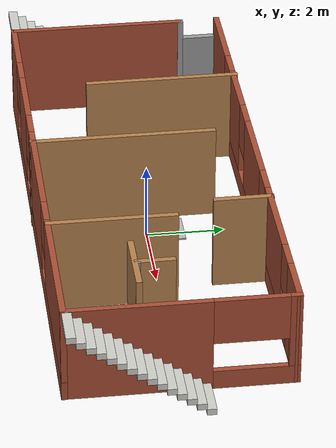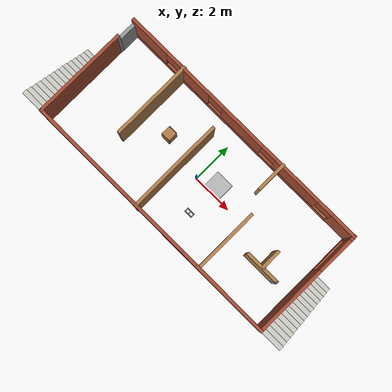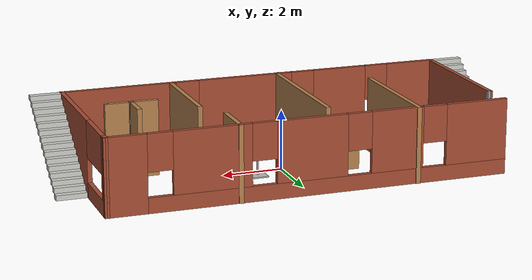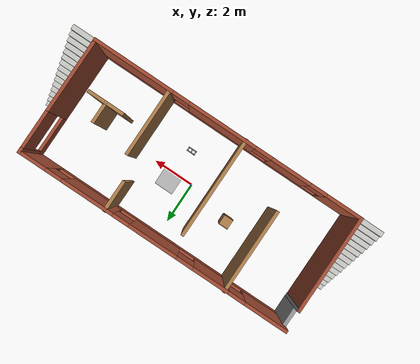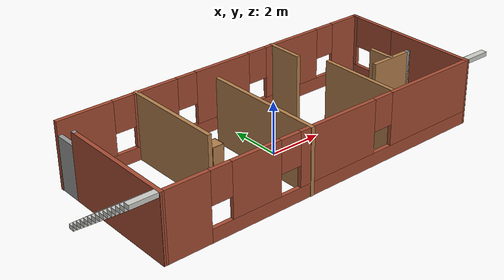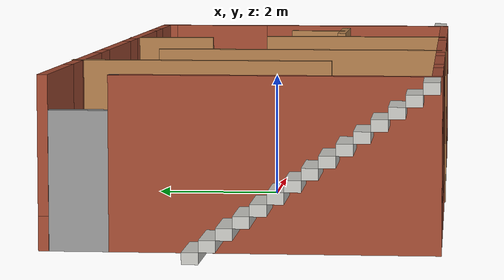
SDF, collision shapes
<?xml version='1.0'?>
<sdf version='1.7'>
  <model name='house1'>
    <link name='Door_0'>
      <pose>-6.52119 2.27125 0 0 -0 1.57228</pose>
      <self_collide>0</self_collide>
      <enable_wind>0</enable_wind>
      <kinematic>0</kinematic>
      <visual name='Door_0_Visual'>
        <pose>0 0 1 0 -0 0</pose>
        <geometry>
          <box>
            <size>0.9 0.17 2</size>
          </box>
        </geometry>
        <material>
          <script>
            <uri>file://media/materials/scripts/gazebo.material</uri>
            <name>Gazebo/Grey</name>
          </script>
          <shader type='pixel'/>
        </material>
        <transparency>0</transparency>
        <cast_shadows>1</cast_shadows>
      </visual>
      <collision name='Door_0_Collision'>
        <laser_retro>0</laser_retro>
        <max_contacts>10</max_contacts>
        <pose>0 0 1 0 -0 0</pose>
        <geometry>
          <box>
            <size>0.9 0.17 2</size>
          </box>
        </geometry>
        <surface>
          <friction>
            <ode>
              <mu>1</mu>
              <mu2>1</mu2>
              <fdir1>0 0 0</fdir1>
              <slip1>0</slip1>
              <slip2>0</slip2>
            </ode>
            <torsional>
              <coefficient>1</coefficient>
              <patch_radius>0</patch_radius>
              <surface_radius>0</surface_radius>
              <use_patch_radius>1</use_patch_radius>
              <ode>
                <slip>0</slip>
              </ode>
            </torsional>
          </friction>
          <bounce>
            <restitution_coefficient>0</restitution_coefficient>
            <threshold>1e+06</threshold>
          </bounce>
          <contact>
            <collide_without_contact>0</collide_without_contact>
            <collide_without_contact_bitmask>1</collide_without_contact_bitmask>
            <collide_bitmask>1</collide_bitmask>
            <ode>
              <soft_cfm>0</soft_cfm>
              <soft_erp>0.2</soft_erp>
              <kp>1e+13</kp>
              <kd>1</kd>
              <max_vel>0.01</max_vel>
              <min_depth>0</min_depth>
            </ode>
            <bullet>
              <split_impulse>1</split_impulse>
              <split_impulse_penetration_threshold>-0.01</split_impulse_penetration_threshold>
              <soft_cfm>0</soft_cfm>
              <soft_erp>0.2</soft_erp>
              <kp>1e+13</kp>
              <kd>1</kd>
            </bullet>
          </contact>
        </surface>
      </collision>
    </link>
    <link name='Stairs_0'>
      <self_collide>0</self_collide>
      <enable_wind>0</enable_wind>
      <kinematic>0</kinematic>
      <pose>0 0 0 0 -0 0</pose>
      <visual name='Stairs_0_Visual_1'>
        <pose>-7.11919 0.32475 0.25 0 -0 0</pose>
        <geometry>
          <box>
            <size>1 0.233333 0.166667</size>
          </box>
        </geometry>
        <material>
          <script>
            <uri>file://media/materials/scripts/gazebo.material</uri>
            <name>Gazebo/CeilingTiled</name>
          </script>
          <ambient>1 1 1 1</ambient>
          <shader type='pixel'/>
        </material>
        <meta>
          <layer>0</layer>
        </meta>
        <transparency>0</transparency>
        <cast_shadows>1</cast_shadows>
      </visual>
      <visual name='Stairs_0_Visual_0'>
        <pose>-7.11919 0.558083 0.083333 0 -0 0</pose>
        <geometry>
          <box>
            <size>1 0.233333 0.166667</size>
          </box>
        </geometry>
        <material>
          <script>
            <uri>file://media/materials/scripts/gazebo.material</uri>
            <name>Gazebo/CeilingTiled</name>
          </script>
          <ambient>1 1 1 1</ambient>
          <shader type='pixel'/>
        </material>
        <meta>
          <layer>0</layer>
        </meta>
        <transparency>0</transparency>
        <cast_shadows>1</cast_shadows>
      </visual>
      <visual name='Stairs_0_Visual_2'>
        <pose>-7.11919 0.091417 0.416667 0 -0 0</pose>
        <geometry>
          <box>
            <size>1 0.233333 0.166667</size>
          </box>
        </geometry>
        <material>
          <script>
            <uri>file://media/materials/scripts/gazebo.material</uri>
            <name>Gazebo/CeilingTiled</name>
          </script>
          <ambient>1 1 1 1</ambient>
          <shader type='pixel'/>
        </material>
        <meta>
          <layer>0</layer>
        </meta>
        <transparency>0</transparency>
        <cast_shadows>1</cast_shadows>
      </visual>
      <visual name='Stairs_0_Visual_3'>
        <pose>-7.11919 -0.141917 0.583333 0 -0 0</pose>
        <geometry>
          <box>
            <size>1 0.233333 0.166667</size>
          </box>
        </geometry>
        <material>
          <script>
            <uri>file://media/materials/scripts/gazebo.material</uri>
            <name>Gazebo/CeilingTiled</name>
          </script>
          <ambient>1 1 1 1</ambient>
          <shader type='pixel'/>
        </material>
        <meta>
          <layer>0</layer>
        </meta>
        <transparency>0</transparency>
        <cast_shadows>1</cast_shadows>
      </visual>
      <visual name='Stairs_0_Visual_4'>
        <pose>-7.11919 -0.37525 0.75 0 -0 0</pose>
        <geometry>
          <box>
            <size>1 0.233333 0.166667</size>
          </box>
        </geometry>
        <material>
          <script>
            <uri>file://media/materials/scripts/gazebo.material</uri>
            <name>Gazebo/CeilingTiled</name>
          </script>
          <ambient>1 1 1 1</ambient>
          <shader type='pixel'/>
        </material>
        <meta>
          <layer>0</layer>
        </meta>
        <transparency>0</transparency>
        <cast_shadows>1</cast_shadows>
      </visual>
      <visual name='Stairs_0_Visual_5'>
        <pose>-7.11919 -0.608583 0.916667 0 -0 0</pose>
        <geometry>
          <box>
            <size>1 0.233333 0.166667</size>
          </box>
        </geometry>
        <material>
          <script>
            <uri>file://media/materials/scripts/gazebo.material</uri>
            <name>Gazebo/CeilingTiled</name>
          </script>
          <ambient>1 1 1 1</ambient>
          <shader type='pixel'/>
        </material>
        <meta>
          <layer>0</layer>
        </meta>
        <transparency>0</transparency>
        <cast_shadows>1</cast_shadows>
      </visual>
      <visual name='Stairs_0_Visual_6'>
        <pose>-7.11919 -0.841917 1.08333 0 -0 0</pose>
        <geometry>
          <box>
            <size>1 0.233333 0.166667</size>
          </box>
        </geometry>
        <material>
          <script>
            <uri>file://media/materials/scripts/gazebo.material</uri>
            <name>Gazebo/CeilingTiled</name>
          </script>
          <ambient>1 1 1 1</ambient>
          <shader type='pixel'/>
        </material>
        <meta>
          <layer>0</layer>
        </meta>
        <transparency>0</transparency>
        <cast_shadows>1</cast_shadows>
      </visual>
      <visual name='Stairs_0_Visual_7'>
        <pose>-7.11919 -1.07525 1.25 0 -0 0</pose>
        <geometry>
          <box>
            <size>1 0.233333 0.166667</size>
          </box>
        </geometry>
        <material>
          <script>
            <uri>file://media/materials/scripts/gazebo.material</uri>
            <name>Gazebo/CeilingTiled</name>
          </script>
          <ambient>1 1 1 1</ambient>
          <shader type='pixel'/>
        </material>
        <meta>
          <layer>0</layer>
        </meta>
        <transparency>0</transparency>
        <cast_shadows>1</cast_shadows>
      </visual>
      <visual name='Stairs_0_Visual_8'>
        <pose>-7.11919 -1.30858 1.41667 0 -0 0</pose>
        <geometry>
          <box>
            <size>1 0.233333 0.166667</size>
          </box>
        </geometry>
        <material>
          <script>
            <uri>file://media/materials/scripts/gazebo.material</uri>
            <name>Gazebo/CeilingTiled</name>
          </script>
          <ambient>1 1 1 1</ambient>
          <shader type='pixel'/>
        </material>
        <meta>
          <layer>0</layer>
        </meta>
        <transparency>0</transparency>
        <cast_shadows>1</cast_shadows>
      </visual>
      <visual name='Stairs_0_Visual_9'>
        <pose>-7.11919 -1.54192 1.58333 0 -0 0</pose>
        <geometry>
          <box>
            <size>1 0.233333 0.166667</size>
          </box>
        </geometry>
        <material>
          <script>
            <uri>file://media/materials/scripts/gazebo.material</uri>
            <name>Gazebo/CeilingTiled</name>
          </script>
          <ambient>1 1 1 1</ambient>
          <shader type='pixel'/>
        </material>
        <meta>
          <layer>0</layer>
        </meta>
        <transparency>0</transparency>
        <cast_shadows>1</cast_shadows>
      </visual>
      <visual name='Stairs_0_Visual_10'>
        <pose>-7.11919 -1.77525 1.75 0 -0 0</pose>
        <geometry>
          <box>
            <size>1 0.233333 0.166667</size>
          </box>
        </geometry>
        <material>
          <script>
            <uri>file://media/materials/scripts/gazebo.material</uri>
            <name>Gazebo/CeilingTiled</name>
          </script>
          <ambient>1 1 1 1</ambient>
          <shader type='pixel'/>
        </material>
        <meta>
          <layer>0</layer>
        </meta>
        <transparency>0</transparency>
        <cast_shadows>1</cast_shadows>
      </visual>
      <visual name='Stairs_0_Visual_11'>
        <pose>-7.11919 -2.00858 1.91667 0 -0 0</pose>
        <geometry>
          <box>
            <size>1 0.233333 0.166667</size>
          </box>
        </geometry>
        <material>
          <script>
            <uri>file://media/materials/scripts/gazebo.material</uri>
            <name>Gazebo/CeilingTiled</name>
          </script>
          <ambient>1 1 1 1</ambient>
          <shader type='pixel'/>
        </material>
        <meta>
          <layer>0</layer>
        </meta>
        <transparency>0</transparency>
        <cast_shadows>1</cast_shadows>
      </visual>
      <visual name='Stairs_0_Visual_12'>
        <pose>-7.11919 -2.24192 2.08333 0 -0 0</pose>
        <geometry>
          <box>
            <size>1 0.233333 0.166667</size>
          </box>
        </geometry>
        <material>
          <script>
            <uri>file://media/materials/scripts/gazebo.material</uri>
            <name>Gazebo/CeilingTiled</name>
          </script>
          <ambient>1 1 1 1</ambient>
          <shader type='pixel'/>
        </material>
        <meta>
          <layer>0</layer>
        </meta>
        <transparency>0</transparency>
        <cast_shadows>1</cast_shadows>
      </visual>
      <visual name='Stairs_0_Visual_13'>
        <pose>-7.11919 -2.47525 2.25 0 -0 0</pose>
        <geometry>
          <box>
            <size>1 0.233333 0.166667</size>
          </box>
        </geometry>
        <material>
          <script>
            <uri>file://media/materials/scripts/gazebo.material</uri>
            <name>Gazebo/CeilingTiled</name>
          </script>
          <ambient>1 1 1 1</ambient>
          <shader type='pixel'/>
        </material>
        <meta>
          <layer>0</layer>
        </meta>
        <transparency>0</transparency>
        <cast_shadows>1</cast_shadows>
      </visual>
      <visual name='Stairs_0_Visual_14'>
        <pose>-7.11919 -2.70858 2.41667 0 -0 0</pose>
        <geometry>
          <box>
            <size>1 0.233333 0.166667</size>
          </box>
        </geometry>
        <material>
          <script>
            <uri>file://media/materials/scripts/gazebo.material</uri>
            <name>Gazebo/CeilingTiled</name>
          </script>
          <ambient>1 1 1 1</ambient>
          <shader type='pixel'/>
        </material>
        <meta>
          <layer>0</layer>
        </meta>
        <transparency>0</transparency>
        <cast_shadows>1</cast_shadows>
      </visual>
      <collision name='Stairs_0_Collision_0'>
        <laser_retro>0</laser_retro>
        <max_contacts>10</max_contacts>
        <pose>-7.11919 0.558083 0.083333 0 -0 0</pose>
        <geometry>
          <box>
            <size>1 0.233333 0.166667</size>
          </box>
        </geometry>
        <surface>
          <friction>
            <ode>
              <mu>1</mu>
              <mu2>1</mu2>
              <fdir1>0 0 0</fdir1>
              <slip1>0</slip1>
              <slip2>0</slip2>
            </ode>
            <torsional>
              <coefficient>1</coefficient>
              <patch_radius>0</patch_radius>
              <surface_radius>0</surface_radius>
              <use_patch_radius>1</use_patch_radius>
              <ode>
                <slip>0</slip>
              </ode>
            </torsional>
          </friction>
          <bounce>
            <restitution_coefficient>0</restitution_coefficient>
            <threshold>1e+06</threshold>
          </bounce>
          <contact>
            <collide_without_contact>0</collide_without_contact>
            <collide_without_contact_bitmask>1</collide_without_contact_bitmask>
            <collide_bitmask>1</collide_bitmask>
            <ode>
              <soft_cfm>0</soft_cfm>
              <soft_erp>0.2</soft_erp>
              <kp>1e+13</kp>
              <kd>1</kd>
              <max_vel>0.01</max_vel>
              <min_depth>0</min_depth>
            </ode>
            <bullet>
              <split_impulse>1</split_impulse>
              <split_impulse_penetration_threshold>-0.01</split_impulse_penetration_threshold>
              <soft_cfm>0</soft_cfm>
              <soft_erp>0.2</soft_erp>
              <kp>1e+13</kp>
              <kd>1</kd>
            </bullet>
          </contact>
        </surface>
      </collision>
      <collision name='Stairs_0_Collision_1'>
        <laser_retro>0</laser_retro>
        <max_contacts>10</max_contacts>
        <pose>-7.11919 0.32475 0.25 0 -0 0</pose>
        <geometry>
          <box>
            <size>1 0.233333 0.166667</size>
          </box>
        </geometry>
        <surface>
          <friction>
            <ode>
              <mu>1</mu>
              <mu2>1</mu2>
              <fdir1>0 0 0</fdir1>
              <slip1>0</slip1>
              <slip2>0</slip2>
            </ode>
            <torsional>
              <coefficient>1</coefficient>
              <patch_radius>0</patch_radius>
              <surface_radius>0</surface_radius>
              <use_patch_radius>1</use_patch_radius>
              <ode>
                <slip>0</slip>
              </ode>
            </torsional>
          </friction>
          <bounce>
            <restitution_coefficient>0</restitution_coefficient>
            <threshold>1e+06</threshold>
          </bounce>
          <contact>
            <collide_without_contact>0</collide_without_contact>
            <collide_without_contact_bitmask>1</collide_without_contact_bitmask>
            <collide_bitmask>1</collide_bitmask>
            <ode>
              <soft_cfm>0</soft_cfm>
              <soft_erp>0.2</soft_erp>
              <kp>1e+13</kp>
              <kd>1</kd>
              <max_vel>0.01</max_vel>
              <min_depth>0</min_depth>
            </ode>
            <bullet>
              <split_impulse>1</split_impulse>
              <split_impulse_penetration_threshold>-0.01</split_impulse_penetration_threshold>
              <soft_cfm>0</soft_cfm>
              <soft_erp>0.2</soft_erp>
              <kp>1e+13</kp>
              <kd>1</kd>
            </bullet>
          </contact>
        </surface>
      </collision>
      <collision name='Stairs_0_Collision_2'>
        <laser_retro>0</laser_retro>
        <max_contacts>10</max_contacts>
        <pose>-7.11919 0.091417 0.416667 0 -0 0</pose>
        <geometry>
          <box>
            <size>1 0.233333 0.166667</size>
          </box>
        </geometry>
        <surface>
          <friction>
            <ode>
              <mu>1</mu>
              <mu2>1</mu2>
              <fdir1>0 0 0</fdir1>
              <slip1>0</slip1>
              <slip2>0</slip2>
            </ode>
            <torsional>
              <coefficient>1</coefficient>
              <patch_radius>0</patch_radius>
              <surface_radius>0</surface_radius>
              <use_patch_radius>1</use_patch_radius>
              <ode>
                <slip>0</slip>
              </ode>
            </torsional>
          </friction>
          <bounce>
            <restitution_coefficient>0</restitution_coefficient>
            <threshold>1e+06</threshold>
          </bounce>
          <contact>
            <collide_without_contact>0</collide_without_contact>
            <collide_without_contact_bitmask>1</collide_without_contact_bitmask>
            <collide_bitmask>1</collide_bitmask>
            <ode>
              <soft_cfm>0</soft_cfm>
              <soft_erp>0.2</soft_erp>
              <kp>1e+13</kp>
              <kd>1</kd>
              <max_vel>0.01</max_vel>
              <min_depth>0</min_depth>
            </ode>
            <bullet>
              <split_impulse>1</split_impulse>
              <split_impulse_penetration_threshold>-0.01</split_impulse_penetration_threshold>
              <soft_cfm>0</soft_cfm>
              <soft_erp>0.2</soft_erp>
              <kp>1e+13</kp>
              <kd>1</kd>
            </bullet>
          </contact>
        </surface>
      </collision>
      <collision name='Stairs_0_Collision_3'>
        <laser_retro>0</laser_retro>
        <max_contacts>10</max_contacts>
        <pose>-7.11919 -0.141917 0.583333 0 -0 0</pose>
        <geometry>
          <box>
            <size>1 0.233333 0.166667</size>
          </box>
        </geometry>
        <surface>
          <friction>
            <ode>
              <mu>1</mu>
              <mu2>1</mu2>
              <fdir1>0 0 0</fdir1>
              <slip1>0</slip1>
              <slip2>0</slip2>
            </ode>
            <torsional>
              <coefficient>1</coefficient>
              <patch_radius>0</patch_radius>
              <surface_radius>0</surface_radius>
              <use_patch_radius>1</use_patch_radius>
              <ode>
                <slip>0</slip>
              </ode>
            </torsional>
          </friction>
          <bounce>
            <restitution_coefficient>0</restitution_coefficient>
            <threshold>1e+06</threshold>
          </bounce>
          <contact>
            <collide_without_contact>0</collide_without_contact>
            <collide_without_contact_bitmask>1</collide_without_contact_bitmask>
            <collide_bitmask>1</collide_bitmask>
            <ode>
              <soft_cfm>0</soft_cfm>
              <soft_erp>0.2</soft_erp>
              <kp>1e+13</kp>
              <kd>1</kd>
              <max_vel>0.01</max_vel>
              <min_depth>0</min_depth>
            </ode>
            <bullet>
              <split_impulse>1</split_impulse>
              <split_impulse_penetration_threshold>-0.01</split_impulse_penetration_threshold>
              <soft_cfm>0</soft_cfm>
              <soft_erp>0.2</soft_erp>
              <kp>1e+13</kp>
              <kd>1</kd>
            </bullet>
          </contact>
        </surface>
      </collision>
      <collision name='Stairs_0_Collision_5'>
        <laser_retro>0</laser_retro>
        <max_contacts>10</max_contacts>
        <pose>-7.11919 -0.608583 0.916667 0 -0 0</pose>
        <geometry>
          <box>
            <size>1 0.233333 0.166667</size>
          </box>
        </geometry>
        <surface>
          <friction>
            <ode>
              <mu>1</mu>
              <mu2>1</mu2>
              <fdir1>0 0 0</fdir1>
              <slip1>0</slip1>
              <slip2>0</slip2>
            </ode>
            <torsional>
              <coefficient>1</coefficient>
              <patch_radius>0</patch_radius>
              <surface_radius>0</surface_radius>
              <use_patch_radius>1</use_patch_radius>
              <ode>
                <slip>0</slip>
              </ode>
            </torsional>
          </friction>
          <bounce>
            <restitution_coefficient>0</restitution_coefficient>
            <threshold>1e+06</threshold>
          </bounce>
          <contact>
            <collide_without_contact>0</collide_without_contact>
            <collide_without_contact_bitmask>1</collide_without_contact_bitmask>
            <collide_bitmask>1</collide_bitmask>
            <ode>
              <soft_cfm>0</soft_cfm>
              <soft_erp>0.2</soft_erp>
              <kp>1e+13</kp>
              <kd>1</kd>
              <max_vel>0.01</max_vel>
              <min_depth>0</min_depth>
            </ode>
            <bullet>
              <split_impulse>1</split_impulse>
              <split_impulse_penetration_threshold>-0.01</split_impulse_penetration_threshold>
              <soft_cfm>0</soft_cfm>
              <soft_erp>0.2</soft_erp>
              <kp>1e+13</kp>
              <kd>1</kd>
            </bullet>
          </contact>
        </surface>
      </collision>
      <collision name='Stairs_0_Collision_4'>
        <laser_retro>0</laser_retro>
        <max_contacts>10</max_contacts>
        <pose>-7.11919 -0.37525 0.75 0 -0 0</pose>
        <geometry>
          <box>
            <size>1 0.233333 0.166667</size>
          </box>
        </geometry>
        <surface>
          <friction>
            <ode>
              <mu>1</mu>
              <mu2>1</mu2>
              <fdir1>0 0 0</fdir1>
              <slip1>0</slip1>
              <slip2>0</slip2>
            </ode>
            <torsional>
              <coefficient>1</coefficient>
              <patch_radius>0</patch_radius>
              <surface_radius>0</surface_radius>
              <use_patch_radius>1</use_patch_radius>
              <ode>
                <slip>0</slip>
              </ode>
            </torsional>
          </friction>
          <bounce>
            <restitution_coefficient>0</restitution_coefficient>
            <threshold>1e+06</threshold>
          </bounce>
          <contact>
            <collide_without_contact>0</collide_without_contact>
            <collide_without_contact_bitmask>1</collide_without_contact_bitmask>
            <collide_bitmask>1</collide_bitmask>
            <ode>
              <soft_cfm>0</soft_cfm>
              <soft_erp>0.2</soft_erp>
              <kp>1e+13</kp>
              <kd>1</kd>
              <max_vel>0.01</max_vel>
              <min_depth>0</min_depth>
            </ode>
            <bullet>
              <split_impulse>1</split_impulse>
              <split_impulse_penetration_threshold>-0.01</split_impulse_penetration_threshold>
              <soft_cfm>0</soft_cfm>
              <soft_erp>0.2</soft_erp>
              <kp>1e+13</kp>
              <kd>1</kd>
            </bullet>
          </contact>
        </surface>
      </collision>
      <collision name='Stairs_0_Collision_6'>
        <laser_retro>0</laser_retro>
        <max_contacts>10</max_contacts>
        <pose>-7.11919 -0.841917 1.08333 0 -0 0</pose>
        <geometry>
          <box>
            <size>1 0.233333 0.166667</size>
          </box>
        </geometry>
        <surface>
          <friction>
            <ode>
              <mu>1</mu>
              <mu2>1</mu2>
              <fdir1>0 0 0</fdir1>
              <slip1>0</slip1>
              <slip2>0</slip2>
            </ode>
            <torsional>
              <coefficient>1</coefficient>
              <patch_radius>0</patch_radius>
              <surface_radius>0</surface_radius>
              <use_patch_radius>1</use_patch_radius>
              <ode>
                <slip>0</slip>
              </ode>
            </torsional>
          </friction>
          <bounce>
            <restitution_coefficient>0</restitution_coefficient>
            <threshold>1e+06</threshold>
          </bounce>
          <contact>
            <collide_without_contact>0</collide_without_contact>
            <collide_without_contact_bitmask>1</collide_without_contact_bitmask>
            <collide_bitmask>1</collide_bitmask>
            <ode>
              <soft_cfm>0</soft_cfm>
              <soft_erp>0.2</soft_erp>
              <kp>1e+13</kp>
              <kd>1</kd>
              <max_vel>0.01</max_vel>
              <min_depth>0</min_depth>
            </ode>
            <bullet>
              <split_impulse>1</split_impulse>
              <split_impulse_penetration_threshold>-0.01</split_impulse_penetration_threshold>
              <soft_cfm>0</soft_cfm>
              <soft_erp>0.2</soft_erp>
              <kp>1e+13</kp>
              <kd>1</kd>
            </bullet>
          </contact>
        </surface>
      </collision>
      <collision name='Stairs_0_Collision_7'>
        <laser_retro>0</laser_retro>
        <max_contacts>10</max_contacts>
        <pose>-7.11919 -1.07525 1.25 0 -0 0</pose>
        <geometry>
          <box>
            <size>1 0.233333 0.166667</size>
          </box>
        </geometry>
        <surface>
          <friction>
            <ode>
              <mu>1</mu>
              <mu2>1</mu2>
              <fdir1>0 0 0</fdir1>
              <slip1>0</slip1>
              <slip2>0</slip2>
            </ode>
            <torsional>
              <coefficient>1</coefficient>
              <patch_radius>0</patch_radius>
              <surface_radius>0</surface_radius>
              <use_patch_radius>1</use_patch_radius>
              <ode>
                <slip>0</slip>
              </ode>
            </torsional>
          </friction>
          <bounce>
            <restitution_coefficient>0</restitution_coefficient>
            <threshold>1e+06</threshold>
          </bounce>
          <contact>
            <collide_without_contact>0</collide_without_contact>
            <collide_without_contact_bitmask>1</collide_without_contact_bitmask>
            <collide_bitmask>1</collide_bitmask>
            <ode>
              <soft_cfm>0</soft_cfm>
              <soft_erp>0.2</soft_erp>
              <kp>1e+13</kp>
              <kd>1</kd>
              <max_vel>0.01</max_vel>
              <min_depth>0</min_depth>
            </ode>
            <bullet>
              <split_impulse>1</split_impulse>
              <split_impulse_penetration_threshold>-0.01</split_impulse_penetration_threshold>
              <soft_cfm>0</soft_cfm>
              <soft_erp>0.2</soft_erp>
              <kp>1e+13</kp>
              <kd>1</kd>
            </bullet>
          </contact>
        </surface>
      </collision>
      <collision name='Stairs_0_Collision_8'>
        <laser_retro>0</laser_retro>
        <max_contacts>10</max_contacts>
        <pose>-7.11919 -1.30858 1.41667 0 -0 0</pose>
        <geometry>
          <box>
            <size>1 0.233333 0.166667</size>
          </box>
        </geometry>
        <surface>
          <friction>
            <ode>
              <mu>1</mu>
              <mu2>1</mu2>
              <fdir1>0 0 0</fdir1>
              <slip1>0</slip1>
              <slip2>0</slip2>
            </ode>
            <torsional>
              <coefficient>1</coefficient>
              <patch_radius>0</patch_radius>
              <surface_radius>0</surface_radius>
              <use_patch_radius>1</use_patch_radius>
              <ode>
                <slip>0</slip>
              </ode>
            </torsional>
          </friction>
          <bounce>
            <restitution_coefficient>0</restitution_coefficient>
            <threshold>1e+06</threshold>
          </bounce>
          <contact>
            <collide_without_contact>0</collide_without_contact>
            <collide_without_contact_bitmask>1</collide_without_contact_bitmask>
            <collide_bitmask>1</collide_bitmask>
            <ode>
              <soft_cfm>0</soft_cfm>
              <soft_erp>0.2</soft_erp>
              <kp>1e+13</kp>
              <kd>1</kd>
              <max_vel>0.01</max_vel>
              <min_depth>0</min_depth>
            </ode>
            <bullet>
              <split_impulse>1</split_impulse>
              <split_impulse_penetration_threshold>-0.01</split_impulse_penetration_threshold>
              <soft_cfm>0</soft_cfm>
              <soft_erp>0.2</soft_erp>
              <kp>1e+13</kp>
              <kd>1</kd>
            </bullet>
          </contact>
        </surface>
      </collision>
      <collision name='Stairs_0_Collision_9'>
        <laser_retro>0</laser_retro>
        <max_contacts>10</max_contacts>
        <pose>-7.11919 -1.54192 1.58333 0 -0 0</pose>
        <geometry>
          <box>
            <size>1 0.233333 0.166667</size>
          </box>
        </geometry>
        <surface>
          <friction>
            <ode>
              <mu>1</mu>
              <mu2>1</mu2>
              <fdir1>0 0 0</fdir1>
              <slip1>0</slip1>
              <slip2>0</slip2>
            </ode>
            <torsional>
              <coefficient>1</coefficient>
              <patch_radius>0</patch_radius>
              <surface_radius>0</surface_radius>
              <use_patch_radius>1</use_patch_radius>
              <ode>
                <slip>0</slip>
              </ode>
            </torsional>
          </friction>
          <bounce>
            <restitution_coefficient>0</restitution_coefficient>
            <threshold>1e+06</threshold>
          </bounce>
          <contact>
            <collide_without_contact>0</collide_without_contact>
            <collide_without_contact_bitmask>1</collide_without_contact_bitmask>
            <collide_bitmask>1</collide_bitmask>
            <ode>
              <soft_cfm>0</soft_cfm>
              <soft_erp>0.2</soft_erp>
              <kp>1e+13</kp>
              <kd>1</kd>
              <max_vel>0.01</max_vel>
              <min_depth>0</min_depth>
            </ode>
            <bullet>
              <split_impulse>1</split_impulse>
              <split_impulse_penetration_threshold>-0.01</split_impulse_penetration_threshold>
              <soft_cfm>0</soft_cfm>
              <soft_erp>0.2</soft_erp>
              <kp>1e+13</kp>
              <kd>1</kd>
            </bullet>
          </contact>
        </surface>
      </collision>
      <collision name='Stairs_0_Collision_10'>
        <laser_retro>0</laser_retro>
        <max_contacts>10</max_contacts>
        <pose>-7.11919 -1.77525 1.75 0 -0 0</pose>
        <geometry>
          <box>
            <size>1 0.233333 0.166667</size>
          </box>
        </geometry>
        <surface>
          <friction>
            <ode>
              <mu>1</mu>
              <mu2>1</mu2>
              <fdir1>0 0 0</fdir1>
              <slip1>0</slip1>
              <slip2>0</slip2>
            </ode>
            <torsional>
              <coefficient>1</coefficient>
              <patch_radius>0</patch_radius>
              <surface_radius>0</surface_radius>
              <use_patch_radius>1</use_patch_radius>
              <ode>
                <slip>0</slip>
              </ode>
            </torsional>
          </friction>
          <bounce>
            <restitution_coefficient>0</restitution_coefficient>
            <threshold>1e+06</threshold>
          </bounce>
          <contact>
            <collide_without_contact>0</collide_without_contact>
            <collide_without_contact_bitmask>1</collide_without_contact_bitmask>
            <collide_bitmask>1</collide_bitmask>
            <ode>
              <soft_cfm>0</soft_cfm>
              <soft_erp>0.2</soft_erp>
              <kp>1e+13</kp>
              <kd>1</kd>
              <max_vel>0.01</max_vel>
              <min_depth>0</min_depth>
            </ode>
            <bullet>
              <split_impulse>1</split_impulse>
              <split_impulse_penetration_threshold>-0.01</split_impulse_penetration_threshold>
              <soft_cfm>0</soft_cfm>
              <soft_erp>0.2</soft_erp>
              <kp>1e+13</kp>
              <kd>1</kd>
            </bullet>
          </contact>
        </surface>
      </collision>
      <collision name='Stairs_0_Collision_11'>
        <laser_retro>0</laser_retro>
        <max_contacts>10</max_contacts>
        <pose>-7.11919 -2.00858 1.91667 0 -0 0</pose>
        <geometry>
          <box>
            <size>1 0.233333 0.166667</size>
          </box>
        </geometry>
        <surface>
          <friction>
            <ode>
              <mu>1</mu>
              <mu2>1</mu2>
              <fdir1>0 0 0</fdir1>
              <slip1>0</slip1>
              <slip2>0</slip2>
            </ode>
            <torsional>
              <coefficient>1</coefficient>
              <patch_radius>0</patch_radius>
              <surface_radius>0</surface_radius>
              <use_patch_radius>1</use_patch_radius>
              <ode>
                <slip>0</slip>
              </ode>
            </torsional>
          </friction>
          <bounce>
            <restitution_coefficient>0</restitution_coefficient>
            <threshold>1e+06</threshold>
          </bounce>
          <contact>
            <collide_without_contact>0</collide_without_contact>
            <collide_without_contact_bitmask>1</collide_without_contact_bitmask>
            <collide_bitmask>1</collide_bitmask>
            <ode>
              <soft_cfm>0</soft_cfm>
              <soft_erp>0.2</soft_erp>
              <kp>1e+13</kp>
              <kd>1</kd>
              <max_vel>0.01</max_vel>
              <min_depth>0</min_depth>
            </ode>
            <bullet>
              <split_impulse>1</split_impulse>
              <split_impulse_penetration_threshold>-0.01</split_impulse_penetration_threshold>
              <soft_cfm>0</soft_cfm>
              <soft_erp>0.2</soft_erp>
              <kp>1e+13</kp>
              <kd>1</kd>
            </bullet>
          </contact>
        </surface>
      </collision>
      <collision name='Stairs_0_Collision_13'>
        <laser_retro>0</laser_retro>
        <max_contacts>10</max_contacts>
        <pose>-7.11919 -2.47525 2.25 0 -0 0</pose>
        <geometry>
          <box>
            <size>1 0.233333 0.166667</size>
          </box>
        </geometry>
        <surface>
          <friction>
            <ode>
              <mu>1</mu>
              <mu2>1</mu2>
              <fdir1>0 0 0</fdir1>
              <slip1>0</slip1>
              <slip2>0</slip2>
            </ode>
            <torsional>
              <coefficient>1</coefficient>
              <patch_radius>0</patch_radius>
              <surface_radius>0</surface_radius>
              <use_patch_radius>1</use_patch_radius>
              <ode>
                <slip>0</slip>
              </ode>
            </torsional>
          </friction>
          <bounce>
            <restitution_coefficient>0</restitution_coefficient>
            <threshold>1e+06</threshold>
          </bounce>
          <contact>
            <collide_without_contact>0</collide_without_contact>
            <collide_without_contact_bitmask>1</collide_without_contact_bitmask>
            <collide_bitmask>1</collide_bitmask>
            <ode>
              <soft_cfm>0</soft_cfm>
              <soft_erp>0.2</soft_erp>
              <kp>1e+13</kp>
              <kd>1</kd>
              <max_vel>0.01</max_vel>
              <min_depth>0</min_depth>
            </ode>
            <bullet>
              <split_impulse>1</split_impulse>
              <split_impulse_penetration_threshold>-0.01</split_impulse_penetration_threshold>
              <soft_cfm>0</soft_cfm>
              <soft_erp>0.2</soft_erp>
              <kp>1e+13</kp>
              <kd>1</kd>
            </bullet>
          </contact>
        </surface>
      </collision>
      <collision name='Stairs_0_Collision_12'>
        <laser_retro>0</laser_retro>
        <max_contacts>10</max_contacts>
        <pose>-7.11919 -2.24192 2.08333 0 -0 0</pose>
        <geometry>
          <box>
            <size>1 0.233333 0.166667</size>
          </box>
        </geometry>
        <surface>
          <friction>
            <ode>
              <mu>1</mu>
              <mu2>1</mu2>
              <fdir1>0 0 0</fdir1>
              <slip1>0</slip1>
              <slip2>0</slip2>
            </ode>
            <torsional>
              <coefficient>1</coefficient>
              <patch_radius>0</patch_radius>
              <surface_radius>0</surface_radius>
              <use_patch_radius>1</use_patch_radius>
              <ode>
                <slip>0</slip>
              </ode>
            </torsional>
          </friction>
          <bounce>
            <restitution_coefficient>0</restitution_coefficient>
            <threshold>1e+06</threshold>
          </bounce>
          <contact>
            <collide_without_contact>0</collide_without_contact>
            <collide_without_contact_bitmask>1</collide_without_contact_bitmask>
            <collide_bitmask>1</collide_bitmask>
            <ode>
              <soft_cfm>0</soft_cfm>
              <soft_erp>0.2</soft_erp>
              <kp>1e+13</kp>
              <kd>1</kd>
              <max_vel>0.01</max_vel>
              <min_depth>0</min_depth>
            </ode>
            <bullet>
              <split_impulse>1</split_impulse>
              <split_impulse_penetration_threshold>-0.01</split_impulse_penetration_threshold>
              <soft_cfm>0</soft_cfm>
              <soft_erp>0.2</soft_erp>
              <kp>1e+13</kp>
              <kd>1</kd>
            </bullet>
          </contact>
        </surface>
      </collision>
      <collision name='Stairs_0_Collision_14'>
        <laser_retro>0</laser_retro>
        <max_contacts>10</max_contacts>
        <pose>-7.11919 -2.70858 2.41667 0 -0 0</pose>
        <geometry>
          <box>
            <size>1 0.233333 0.166667</size>
          </box>
        </geometry>
        <surface>
          <friction>
            <ode>
              <mu>1</mu>
              <mu2>1</mu2>
              <fdir1>0 0 0</fdir1>
              <slip1>0</slip1>
              <slip2>0</slip2>
            </ode>
            <torsional>
              <coefficient>1</coefficient>
              <patch_radius>0</patch_radius>
              <surface_radius>0</surface_radius>
              <use_patch_radius>1</use_patch_radius>
              <ode>
                <slip>0</slip>
              </ode>
            </torsional>
          </friction>
          <bounce>
            <restitution_coefficient>0</restitution_coefficient>
            <threshold>1e+06</threshold>
          </bounce>
          <contact>
            <collide_without_contact>0</collide_without_contact>
            <collide_without_contact_bitmask>1</collide_without_contact_bitmask>
            <collide_bitmask>1</collide_bitmask>
            <ode>
              <soft_cfm>0</soft_cfm>
              <soft_erp>0.2</soft_erp>
              <kp>1e+13</kp>
              <kd>1</kd>
              <max_vel>0.01</max_vel>
              <min_depth>0</min_depth>
            </ode>
            <bullet>
              <split_impulse>1</split_impulse>
              <split_impulse_penetration_threshold>-0.01</split_impulse_penetration_threshold>
              <soft_cfm>0</soft_cfm>
              <soft_erp>0.2</soft_erp>
              <kp>1e+13</kp>
              <kd>1</kd>
            </bullet>
          </contact>
        </surface>
      </collision>
    </link>
    <link name='Stairs_1'>
      <self_collide>0</self_collide>
      <enable_wind>0</enable_wind>
      <kinematic>0</kinematic>
      <pose>0 0 0 0 -0 0</pose>
      <visual name='Stairs_1_Visual_0'>
        <pose>7.11919 0.575699 0.083333 0 -0 0</pose>
        <geometry>
          <box>
            <size>1 0.233333 0.166667</size>
          </box>
        </geometry>
        <material>
          <script>
            <uri>file://media/materials/scripts/gazebo.material</uri>
            <name>Gazebo/CeilingTiled</name>
          </script>
          <ambient>1 1 1 1</ambient>
          <shader type='pixel'/>
        </material>
        <meta>
          <layer>0</layer>
        </meta>
        <transparency>0</transparency>
        <cast_shadows>1</cast_shadows>
      </visual>
      <visual name='Stairs_1_Visual_1'>
        <pose>7.11919 0.342365 0.25 0 -0 0</pose>
        <geometry>
          <box>
            <size>1 0.233333 0.166667</size>
          </box>
        </geometry>
        <material>
          <script>
            <uri>file://media/materials/scripts/gazebo.material</uri>
            <name>Gazebo/CeilingTiled</name>
          </script>
          <ambient>1 1 1 1</ambient>
          <shader type='pixel'/>
        </material>
        <meta>
          <layer>0</layer>
        </meta>
        <transparency>0</transparency>
        <cast_shadows>1</cast_shadows>
      </visual>
      <visual name='Stairs_1_Visual_2'>
        <pose>7.11919 0.109032 0.416667 0 -0 0</pose>
        <geometry>
          <box>
            <size>1 0.233333 0.166667</size>
          </box>
        </geometry>
        <material>
          <script>
            <uri>file://media/materials/scripts/gazebo.material</uri>
            <name>Gazebo/CeilingTiled</name>
          </script>
          <ambient>1 1 1 1</ambient>
          <shader type='pixel'/>
        </material>
        <meta>
          <layer>0</layer>
        </meta>
        <transparency>0</transparency>
        <cast_shadows>1</cast_shadows>
      </visual>
      <visual name='Stairs_1_Visual_3'>
        <pose>7.11919 -0.124301 0.583333 0 -0 0</pose>
        <geometry>
          <box>
            <size>1 0.233333 0.166667</size>
          </box>
        </geometry>
        <material>
          <script>
            <uri>file://media/materials/scripts/gazebo.material</uri>
            <name>Gazebo/CeilingTiled</name>
          </script>
          <ambient>1 1 1 1</ambient>
          <shader type='pixel'/>
        </material>
        <meta>
          <layer>0</layer>
        </meta>
        <transparency>0</transparency>
        <cast_shadows>1</cast_shadows>
      </visual>
      <visual name='Stairs_1_Visual_4'>
        <pose>7.11919 -0.357634 0.75 0 -0 0</pose>
        <geometry>
          <box>
            <size>1 0.233333 0.166667</size>
          </box>
        </geometry>
        <material>
          <script>
            <uri>file://media/materials/scripts/gazebo.material</uri>
            <name>Gazebo/CeilingTiled</name>
          </script>
          <ambient>1 1 1 1</ambient>
          <shader type='pixel'/>
        </material>
        <meta>
          <layer>0</layer>
        </meta>
        <transparency>0</transparency>
        <cast_shadows>1</cast_shadows>
      </visual>
      <visual name='Stairs_1_Visual_5'>
        <pose>7.11919 -0.590968 0.916667 0 -0 0</pose>
        <geometry>
          <box>
            <size>1 0.233333 0.166667</size>
          </box>
        </geometry>
        <material>
          <script>
            <uri>file://media/materials/scripts/gazebo.material</uri>
            <name>Gazebo/CeilingTiled</name>
          </script>
          <ambient>1 1 1 1</ambient>
          <shader type='pixel'/>
        </material>
        <meta>
          <layer>0</layer>
        </meta>
        <transparency>0</transparency>
        <cast_shadows>1</cast_shadows>
      </visual>
      <visual name='Stairs_1_Visual_6'>
        <pose>7.11919 -0.824301 1.08333 0 -0 0</pose>
        <geometry>
          <box>
            <size>1 0.233333 0.166667</size>
          </box>
        </geometry>
        <material>
          <script>
            <uri>file://media/materials/scripts/gazebo.material</uri>
            <name>Gazebo/CeilingTiled</name>
          </script>
          <ambient>1 1 1 1</ambient>
          <shader type='pixel'/>
        </material>
        <meta>
          <layer>0</layer>
        </meta>
        <transparency>0</transparency>
        <cast_shadows>1</cast_shadows>
      </visual>
      <visual name='Stairs_1_Visual_7'>
        <pose>7.11919 -1.05763 1.25 0 -0 0</pose>
        <geometry>
          <box>
            <size>1 0.233333 0.166667</size>
          </box>
        </geometry>
        <material>
          <script>
            <uri>file://media/materials/scripts/gazebo.material</uri>
            <name>Gazebo/CeilingTiled</name>
          </script>
          <ambient>1 1 1 1</ambient>
          <shader type='pixel'/>
        </material>
        <meta>
          <layer>0</layer>
        </meta>
        <transparency>0</transparency>
        <cast_shadows>1</cast_shadows>
      </visual>
      <visual name='Stairs_1_Visual_8'>
        <pose>7.11919 -1.29097 1.41667 0 -0 0</pose>
        <geometry>
          <box>
            <size>1 0.233333 0.166667</size>
          </box>
        </geometry>
        <material>
          <script>
            <uri>file://media/materials/scripts/gazebo.material</uri>
            <name>Gazebo/CeilingTiled</name>
          </script>
          <ambient>1 1 1 1</ambient>
          <shader type='pixel'/>
        </material>
        <meta>
          <layer>0</layer>
        </meta>
        <transparency>0</transparency>
        <cast_shadows>1</cast_shadows>
      </visual>
      <visual name='Stairs_1_Visual_9'>
        <pose>7.11919 -1.5243 1.58333 0 -0 0</pose>
        <geometry>
          <box>
            <size>1 0.233333 0.166667</size>
          </box>
        </geometry>
        <material>
          <script>
            <uri>file://media/materials/scripts/gazebo.material</uri>
            <name>Gazebo/CeilingTiled</name>
          </script>
          <ambient>1 1 1 1</ambient>
          <shader type='pixel'/>
        </material>
        <meta>
          <layer>0</layer>
        </meta>
        <transparency>0</transparency>
        <cast_shadows>1</cast_shadows>
      </visual>
      <visual name='Stairs_1_Visual_10'>
        <pose>7.11919 -1.75763 1.75 0 -0 0</pose>
        <geometry>
          <box>
            <size>1 0.233333 0.166667</size>
          </box>
        </geometry>
        <material>
          <script>
            <uri>file://media/materials/scripts/gazebo.material</uri>
            <name>Gazebo/CeilingTiled</name>
          </script>
          <ambient>1 1 1 1</ambient>
          <shader type='pixel'/>
        </material>
        <meta>
          <layer>0</layer>
        </meta>
        <transparency>0</transparency>
        <cast_shadows>1</cast_shadows>
      </visual>
      <visual name='Stairs_1_Visual_11'>
        <pose>7.11919 -1.99097 1.91667 0 -0 0</pose>
        <geometry>
          <box>
            <size>1 0.233333 0.166667</size>
          </box>
        </geometry>
        <material>
          <script>
            <uri>file://media/materials/scripts/gazebo.material</uri>
            <name>Gazebo/CeilingTiled</name>
          </script>
          <ambient>1 1 1 1</ambient>
          <shader type='pixel'/>
        </material>
        <meta>
          <layer>0</layer>
        </meta>
        <transparency>0</transparency>
        <cast_shadows>1</cast_shadows>
      </visual>
      <visual name='Stairs_1_Visual_12'>
        <pose>7.11919 -2.2243 2.08333 0 -0 0</pose>
        <geometry>
          <box>
            <size>1 0.233333 0.166667</size>
          </box>
        </geometry>
        <material>
          <script>
            <uri>file://media/materials/scripts/gazebo.material</uri>
            <name>Gazebo/CeilingTiled</name>
          </script>
          <ambient>1 1 1 1</ambient>
          <shader type='pixel'/>
        </material>
        <meta>
          <layer>0</layer>
        </meta>
        <transparency>0</transparency>
        <cast_shadows>1</cast_shadows>
      </visual>
      <visual name='Stairs_1_Visual_13'>
        <pose>7.11919 -2.45763 2.25 0 -0 0</pose>
        <geometry>
          <box>
            <size>1 0.233333 0.166667</size>
          </box>
        </geometry>
        <material>
          <script>
            <uri>file://media/materials/scripts/gazebo.material</uri>
            <name>Gazebo/CeilingTiled</name>
          </script>
          <ambient>1 1 1 1</ambient>
          <shader type='pixel'/>
        </material>
        <meta>
          <layer>0</layer>
        </meta>
        <transparency>0</transparency>
        <cast_shadows>1</cast_shadows>
      </visual>
      <visual name='Stairs_1_Visual_14'>
        <pose>7.11919 -2.69097 2.41667 0 -0 0</pose>
        <geometry>
          <box>
            <size>1 0.233333 0.166667</size>
          </box>
        </geometry>
        <material>
          <script>
            <uri>file://media/materials/scripts/gazebo.material</uri>
            <name>Gazebo/CeilingTiled</name>
          </script>
          <ambient>1 1 1 1</ambient>
          <shader type='pixel'/>
        </material>
        <meta>
          <layer>0</layer>
        </meta>
        <transparency>0</transparency>
        <cast_shadows>1</cast_shadows>
      </visual>
      <collision name='Stairs_1_Collision_2'>
        <laser_retro>0</laser_retro>
        <max_contacts>10</max_contacts>
        <pose>7.11919 0.109032 0.416667 0 -0 0</pose>
        <geometry>
          <box>
            <size>1 0.233333 0.166667</size>
          </box>
        </geometry>
        <surface>
          <friction>
            <ode>
              <mu>1</mu>
              <mu2>1</mu2>
              <fdir1>0 0 0</fdir1>
              <slip1>0</slip1>
              <slip2>0</slip2>
            </ode>
            <torsional>
              <coefficient>1</coefficient>
              <patch_radius>0</patch_radius>
              <surface_radius>0</surface_radius>
              <use_patch_radius>1</use_patch_radius>
              <ode>
                <slip>0</slip>
              </ode>
            </torsional>
          </friction>
          <bounce>
            <restitution_coefficient>0</restitution_coefficient>
            <threshold>1e+06</threshold>
          </bounce>
          <contact>
            <collide_without_contact>0</collide_without_contact>
            <collide_without_contact_bitmask>1</collide_without_contact_bitmask>
            <collide_bitmask>1</collide_bitmask>
            <ode>
              <soft_cfm>0</soft_cfm>
              <soft_erp>0.2</soft_erp>
              <kp>1e+13</kp>
              <kd>1</kd>
              <max_vel>0.01</max_vel>
              <min_depth>0</min_depth>
            </ode>
            <bullet>
              <split_impulse>1</split_impulse>
              <split_impulse_penetration_threshold>-0.01</split_impulse_penetration_threshold>
              <soft_cfm>0</soft_cfm>
              <soft_erp>0.2</soft_erp>
              <kp>1e+13</kp>
              <kd>1</kd>
            </bullet>
          </contact>
        </surface>
      </collision>
      <collision name='Stairs_1_Collision_0'>
        <laser_retro>0</laser_retro>
        <max_contacts>10</max_contacts>
        <pose>7.11919 0.575699 0.083333 0 -0 0</pose>
        <geometry>
          <box>
            <size>1 0.233333 0.166667</size>
          </box>
        </geometry>
        <surface>
          <friction>
            <ode>
              <mu>1</mu>
              <mu2>1</mu2>
              <fdir1>0 0 0</fdir1>
              <slip1>0</slip1>
              <slip2>0</slip2>
            </ode>
            <torsional>
              <coefficient>1</coefficient>
              <patch_radius>0</patch_radius>
              <surface_radius>0</surface_radius>
              <use_patch_radius>1</use_patch_radius>
              <ode>
                <slip>0</slip>
              </ode>
            </torsional>
          </friction>
          <bounce>
            <restitution_coefficient>0</restitution_coefficient>
            <threshold>1e+06</threshold>
          </bounce>
          <contact>
            <collide_without_contact>0</collide_without_contact>
            <collide_without_contact_bitmask>1</collide_without_contact_bitmask>
            <collide_bitmask>1</collide_bitmask>
            <ode>
              <soft_cfm>0</soft_cfm>
              <soft_erp>0.2</soft_erp>
              <kp>1e+13</kp>
              <kd>1</kd>
              <max_vel>0.01</max_vel>
              <min_depth>0</min_depth>
            </ode>
            <bullet>
              <split_impulse>1</split_impulse>
              <split_impulse_penetration_threshold>-0.01</split_impulse_penetration_threshold>
              <soft_cfm>0</soft_cfm>
              <soft_erp>0.2</soft_erp>
              <kp>1e+13</kp>
              <kd>1</kd>
            </bullet>
          </contact>
        </surface>
      </collision>
      <collision name='Stairs_1_Collision_1'>
        <laser_retro>0</laser_retro>
        <max_contacts>10</max_contacts>
        <pose>7.11919 0.342365 0.25 0 -0 0</pose>
        <geometry>
          <box>
            <size>1 0.233333 0.166667</size>
          </box>
        </geometry>
        <surface>
          <friction>
            <ode>
              <mu>1</mu>
              <mu2>1</mu2>
              <fdir1>0 0 0</fdir1>
              <slip1>0</slip1>
              <slip2>0</slip2>
            </ode>
            <torsional>
              <coefficient>1</coefficient>
              <patch_radius>0</patch_radius>
              <surface_radius>0</surface_radius>
              <use_patch_radius>1</use_patch_radius>
              <ode>
                <slip>0</slip>
              </ode>
            </torsional>
          </friction>
          <bounce>
            <restitution_coefficient>0</restitution_coefficient>
            <threshold>1e+06</threshold>
          </bounce>
          <contact>
            <collide_without_contact>0</collide_without_contact>
            <collide_without_contact_bitmask>1</collide_without_contact_bitmask>
            <collide_bitmask>1</collide_bitmask>
            <ode>
              <soft_cfm>0</soft_cfm>
              <soft_erp>0.2</soft_erp>
              <kp>1e+13</kp>
              <kd>1</kd>
              <max_vel>0.01</max_vel>
              <min_depth>0</min_depth>
            </ode>
            <bullet>
              <split_impulse>1</split_impulse>
              <split_impulse_penetration_threshold>-0.01</split_impulse_penetration_threshold>
              <soft_cfm>0</soft_cfm>
              <soft_erp>0.2</soft_erp>
              <kp>1e+13</kp>
              <kd>1</kd>
            </bullet>
          </contact>
        </surface>
      </collision>
      <collision name='Stairs_1_Collision_3'>
        <laser_retro>0</laser_retro>
        <max_contacts>10</max_contacts>
        <pose>7.11919 -0.124301 0.583333 0 -0 0</pose>
        <geometry>
          <box>
            <size>1 0.233333 0.166667</size>
          </box>
        </geometry>
        <surface>
          <friction>
            <ode>
              <mu>1</mu>
              <mu2>1</mu2>
              <fdir1>0 0 0</fdir1>
              <slip1>0</slip1>
              <slip2>0</slip2>
            </ode>
            <torsional>
              <coefficient>1</coefficient>
              <patch_radius>0</patch_radius>
              <surface_radius>0</surface_radius>
              <use_patch_radius>1</use_patch_radius>
              <ode>
                <slip>0</slip>
              </ode>
            </torsional>
          </friction>
          <bounce>
            <restitution_coefficient>0</restitution_coefficient>
            <threshold>1e+06</threshold>
          </bounce>
          <contact>
            <collide_without_contact>0</collide_without_contact>
            <collide_without_contact_bitmask>1</collide_without_contact_bitmask>
            <collide_bitmask>1</collide_bitmask>
            <ode>
              <soft_cfm>0</soft_cfm>
              <soft_erp>0.2</soft_erp>
              <kp>1e+13</kp>
              <kd>1</kd>
              <max_vel>0.01</max_vel>
              <min_depth>0</min_depth>
            </ode>
            <bullet>
              <split_impulse>1</split_impulse>
              <split_impulse_penetration_threshold>-0.01</split_impulse_penetration_threshold>
              <soft_cfm>0</soft_cfm>
              <soft_erp>0.2</soft_erp>
              <kp>1e+13</kp>
              <kd>1</kd>
            </bullet>
          </contact>
        </surface>
      </collision>
      <collision name='Stairs_1_Collision_4'>
        <laser_retro>0</laser_retro>
        <max_contacts>10</max_contacts>
        <pose>7.11919 -0.357634 0.75 0 -0 0</pose>
        <geometry>
          <box>
            <size>1 0.233333 0.166667</size>
          </box>
        </geometry>
        <surface>
          <friction>
            <ode>
              <mu>1</mu>
              <mu2>1</mu2>
              <fdir1>0 0 0</fdir1>
              <slip1>0</slip1>
              <slip2>0</slip2>
            </ode>
            <torsional>
              <coefficient>1</coefficient>
              <patch_radius>0</patch_radius>
              <surface_radius>0</surface_radius>
              <use_patch_radius>1</use_patch_radius>
              <ode>
                <slip>0</slip>
              </ode>
            </torsional>
          </friction>
          <bounce>
            <restitution_coefficient>0</restitution_coefficient>
            <threshold>1e+06</threshold>
          </bounce>
          <contact>
            <collide_without_contact>0</collide_without_contact>
            <collide_without_contact_bitmask>1</collide_without_contact_bitmask>
            <collide_bitmask>1</collide_bitmask>
            <ode>
              <soft_cfm>0</soft_cfm>
              <soft_erp>0.2</soft_erp>
              <kp>1e+13</kp>
              <kd>1</kd>
              <max_vel>0.01</max_vel>
              <min_depth>0</min_depth>
            </ode>
            <bullet>
              <split_impulse>1</split_impulse>
              <split_impulse_penetration_threshold>-0.01</split_impulse_penetration_threshold>
              <soft_cfm>0</soft_cfm>
              <soft_erp>0.2</soft_erp>
              <kp>1e+13</kp>
              <kd>1</kd>
            </bullet>
          </contact>
        </surface>
      </collision>
      <collision name='Stairs_1_Collision_5'>
        <laser_retro>0</laser_retro>
        <max_contacts>10</max_contacts>
        <pose>7.11919 -0.590968 0.916667 0 -0 0</pose>
        <geometry>
          <box>
            <size>1 0.233333 0.166667</size>
          </box>
        </geometry>
        <surface>
          <friction>
            <ode>
              <mu>1</mu>
              <mu2>1</mu2>
              <fdir1>0 0 0</fdir1>
              <slip1>0</slip1>
              <slip2>0</slip2>
            </ode>
            <torsional>
              <coefficient>1</coefficient>
              <patch_radius>0</patch_radius>
              <surface_radius>0</surface_radius>
              <use_patch_radius>1</use_patch_radius>
              <ode>
                <slip>0</slip>
              </ode>
            </torsional>
          </friction>
          <bounce>
            <restitution_coefficient>0</restitution_coefficient>
            <threshold>1e+06</threshold>
          </bounce>
          <contact>
            <collide_without_contact>0</collide_without_contact>
            <collide_without_contact_bitmask>1</collide_without_contact_bitmask>
            <collide_bitmask>1</collide_bitmask>
            <ode>
              <soft_cfm>0</soft_cfm>
              <soft_erp>0.2</soft_erp>
              <kp>1e+13</kp>
              <kd>1</kd>
              <max_vel>0.01</max_vel>
              <min_depth>0</min_depth>
            </ode>
            <bullet>
              <split_impulse>1</split_impulse>
              <split_impulse_penetration_threshold>-0.01</split_impulse_penetration_threshold>
              <soft_cfm>0</soft_cfm>
              <soft_erp>0.2</soft_erp>
              <kp>1e+13</kp>
              <kd>1</kd>
            </bullet>
          </contact>
        </surface>
      </collision>
      <collision name='Stairs_1_Collision_6'>
        <laser_retro>0</laser_retro>
        <max_contacts>10</max_contacts>
        <pose>7.11919 -0.824301 1.08333 0 -0 0</pose>
        <geometry>
          <box>
            <size>1 0.233333 0.166667</size>
          </box>
        </geometry>
        <surface>
          <friction>
            <ode>
              <mu>1</mu>
              <mu2>1</mu2>
              <fdir1>0 0 0</fdir1>
              <slip1>0</slip1>
              <slip2>0</slip2>
            </ode>
            <torsional>
              <coefficient>1</coefficient>
              <patch_radius>0</patch_radius>
              <surface_radius>0</surface_radius>
              <use_patch_radius>1</use_patch_radius>
              <ode>
                <slip>0</slip>
              </ode>
            </torsional>
          </friction>
          <bounce>
            <restitution_coefficient>0</restitution_coefficient>
            <threshold>1e+06</threshold>
          </bounce>
          <contact>
            <collide_without_contact>0</collide_without_contact>
            <collide_without_contact_bitmask>1</collide_without_contact_bitmask>
            <collide_bitmask>1</collide_bitmask>
            <ode>
              <soft_cfm>0</soft_cfm>
              <soft_erp>0.2</soft_erp>
              <kp>1e+13</kp>
              <kd>1</kd>
              <max_vel>0.01</max_vel>
              <min_depth>0</min_depth>
            </ode>
            <bullet>
              <split_impulse>1</split_impulse>
              <split_impulse_penetration_threshold>-0.01</split_impulse_penetration_threshold>
              <soft_cfm>0</soft_cfm>
              <soft_erp>0.2</soft_erp>
              <kp>1e+13</kp>
              <kd>1</kd>
            </bullet>
          </contact>
        </surface>
      </collision>
      <collision name='Stairs_1_Collision_7'>
        <laser_retro>0</laser_retro>
        <max_contacts>10</max_contacts>
        <pose>7.11919 -1.05763 1.25 0 -0 0</pose>
        <geometry>
          <box>
            <size>1 0.233333 0.166667</size>
          </box>
        </geometry>
        <surface>
          <friction>
            <ode>
              <mu>1</mu>
              <mu2>1</mu2>
              <fdir1>0 0 0</fdir1>
              <slip1>0</slip1>
              <slip2>0</slip2>
            </ode>
            <torsional>
              <coefficient>1</coefficient>
              <patch_radius>0</patch_radius>
              <surface_radius>0</surface_radius>
              <use_patch_radius>1</use_patch_radius>
              <ode>
                <slip>0</slip>
              </ode>
            </torsional>
          </friction>
          <bounce>
            <restitution_coefficient>0</restitution_coefficient>
            <threshold>1e+06</threshold>
          </bounce>
          <contact>
            <collide_without_contact>0</collide_without_contact>
            <collide_without_contact_bitmask>1</collide_without_contact_bitmask>
            <collide_bitmask>1</collide_bitmask>
            <ode>
              <soft_cfm>0</soft_cfm>
              <soft_erp>0.2</soft_erp>
              <kp>1e+13</kp>
              <kd>1</kd>
              <max_vel>0.01</max_vel>
              <min_depth>0</min_depth>
            </ode>
            <bullet>
              <split_impulse>1</split_impulse>
              <split_impulse_penetration_threshold>-0.01</split_impulse_penetration_threshold>
              <soft_cfm>0</soft_cfm>
              <soft_erp>0.2</soft_erp>
              <kp>1e+13</kp>
              <kd>1</kd>
            </bullet>
          </contact>
        </surface>
      </collision>
      <collision name='Stairs_1_Collision_8'>
        <laser_retro>0</laser_retro>
        <max_contacts>10</max_contacts>
        <pose>7.11919 -1.29097 1.41667 0 -0 0</pose>
        <geometry>
          <box>
            <size>1 0.233333 0.166667</size>
          </box>
        </geometry>
        <surface>
          <friction>
            <ode>
              <mu>1</mu>
              <mu2>1</mu2>
              <fdir1>0 0 0</fdir1>
              <slip1>0</slip1>
              <slip2>0</slip2>
            </ode>
            <torsional>
              <coefficient>1</coefficient>
              <patch_radius>0</patch_radius>
              <surface_radius>0</surface_radius>
              <use_patch_radius>1</use_patch_radius>
              <ode>
                <slip>0</slip>
              </ode>
            </torsional>
          </friction>
          <bounce>
            <restitution_coefficient>0</restitution_coefficient>
            <threshold>1e+06</threshold>
          </bounce>
          <contact>
            <collide_without_contact>0</collide_without_contact>
            <collide_without_contact_bitmask>1</collide_without_contact_bitmask>
            <collide_bitmask>1</collide_bitmask>
            <ode>
              <soft_cfm>0</soft_cfm>
              <soft_erp>0.2</soft_erp>
              <kp>1e+13</kp>
              <kd>1</kd>
              <max_vel>0.01</max_vel>
              <min_depth>0</min_depth>
            </ode>
            <bullet>
              <split_impulse>1</split_impulse>
              <split_impulse_penetration_threshold>-0.01</split_impulse_penetration_threshold>
              <soft_cfm>0</soft_cfm>
              <soft_erp>0.2</soft_erp>
              <kp>1e+13</kp>
              <kd>1</kd>
            </bullet>
          </contact>
        </surface>
      </collision>
      <collision name='Stairs_1_Collision_9'>
        <laser_retro>0</laser_retro>
        <max_contacts>10</max_contacts>
        <pose>7.11919 -1.5243 1.58333 0 -0 0</pose>
        <geometry>
          <box>
            <size>1 0.233333 0.166667</size>
          </box>
        </geometry>
        <surface>
          <friction>
            <ode>
              <mu>1</mu>
              <mu2>1</mu2>
              <fdir1>0 0 0</fdir1>
              <slip1>0</slip1>
              <slip2>0</slip2>
            </ode>
            <torsional>
              <coefficient>1</coefficient>
              <patch_radius>0</patch_radius>
              <surface_radius>0</surface_radius>
              <use_patch_radius>1</use_patch_radius>
              <ode>
                <slip>0</slip>
              </ode>
            </torsional>
          </friction>
          <bounce>
            <restitution_coefficient>0</restitution_coefficient>
            <threshold>1e+06</threshold>
          </bounce>
          <contact>
            <collide_without_contact>0</collide_without_contact>
            <collide_without_contact_bitmask>1</collide_without_contact_bitmask>
            <collide_bitmask>1</collide_bitmask>
            <ode>
              <soft_cfm>0</soft_cfm>
              <soft_erp>0.2</soft_erp>
              <kp>1e+13</kp>
              <kd>1</kd>
              <max_vel>0.01</max_vel>
              <min_depth>0</min_depth>
            </ode>
            <bullet>
              <split_impulse>1</split_impulse>
              <split_impulse_penetration_threshold>-0.01</split_impulse_penetration_threshold>
              <soft_cfm>0</soft_cfm>
              <soft_erp>0.2</soft_erp>
              <kp>1e+13</kp>
              <kd>1</kd>
            </bullet>
          </contact>
        </surface>
      </collision>
      <collision name='Stairs_1_Collision_10'>
        <laser_retro>0</laser_retro>
        <max_contacts>10</max_contacts>
        <pose>7.11919 -1.75763 1.75 0 -0 0</pose>
        <geometry>
          <box>
            <size>1 0.233333 0.166667</size>
          </box>
        </geometry>
        <surface>
          <friction>
            <ode>
              <mu>1</mu>
              <mu2>1</mu2>
              <fdir1>0 0 0</fdir1>
              <slip1>0</slip1>
              <slip2>0</slip2>
            </ode>
            <torsional>
              <coefficient>1</coefficient>
              <patch_radius>0</patch_radius>
              <surface_radius>0</surface_radius>
              <use_patch_radius>1</use_patch_radius>
              <ode>
                <slip>0</slip>
              </ode>
            </torsional>
          </friction>
          <bounce>
            <restitution_coefficient>0</restitution_coefficient>
            <threshold>1e+06</threshold>
          </bounce>
          <contact>
            <collide_without_contact>0</collide_without_contact>
            <collide_without_contact_bitmask>1</collide_without_contact_bitmask>
            <collide_bitmask>1</collide_bitmask>
            <ode>
              <soft_cfm>0</soft_cfm>
              <soft_erp>0.2</soft_erp>
              <kp>1e+13</kp>
              <kd>1</kd>
              <max_vel>0.01</max_vel>
              <min_depth>0</min_depth>
            </ode>
            <bullet>
              <split_impulse>1</split_impulse>
              <split_impulse_penetration_threshold>-0.01</split_impulse_penetration_threshold>
              <soft_cfm>0</soft_cfm>
              <soft_erp>0.2</soft_erp>
              <kp>1e+13</kp>
              <kd>1</kd>
            </bullet>
          </contact>
        </surface>
      </collision>
      <collision name='Stairs_1_Collision_11'>
        <laser_retro>0</laser_retro>
        <max_contacts>10</max_contacts>
        <pose>7.11919 -1.99097 1.91667 0 -0 0</pose>
        <geometry>
          <box>
            <size>1 0.233333 0.166667</size>
          </box>
        </geometry>
        <surface>
          <friction>
            <ode>
              <mu>1</mu>
              <mu2>1</mu2>
              <fdir1>0 0 0</fdir1>
              <slip1>0</slip1>
              <slip2>0</slip2>
            </ode>
            <torsional>
              <coefficient>1</coefficient>
              <patch_radius>0</patch_radius>
              <surface_radius>0</surface_radius>
              <use_patch_radius>1</use_patch_radius>
              <ode>
                <slip>0</slip>
              </ode>
            </torsional>
          </friction>
          <bounce>
            <restitution_coefficient>0</restitution_coefficient>
            <threshold>1e+06</threshold>
          </bounce>
          <contact>
            <collide_without_contact>0</collide_without_contact>
            <collide_without_contact_bitmask>1</collide_without_contact_bitmask>
            <collide_bitmask>1</collide_bitmask>
            <ode>
              <soft_cfm>0</soft_cfm>
              <soft_erp>0.2</soft_erp>
              <kp>1e+13</kp>
              <kd>1</kd>
              <max_vel>0.01</max_vel>
              <min_depth>0</min_depth>
            </ode>
            <bullet>
              <split_impulse>1</split_impulse>
              <split_impulse_penetration_threshold>-0.01</split_impulse_penetration_threshold>
              <soft_cfm>0</soft_cfm>
              <soft_erp>0.2</soft_erp>
              <kp>1e+13</kp>
              <kd>1</kd>
            </bullet>
          </contact>
        </surface>
      </collision>
      <collision name='Stairs_1_Collision_12'>
        <laser_retro>0</laser_retro>
        <max_contacts>10</max_contacts>
        <pose>7.11919 -2.2243 2.08333 0 -0 0</pose>
        <geometry>
          <box>
            <size>1 0.233333 0.166667</size>
          </box>
        </geometry>
        <surface>
          <friction>
            <ode>
              <mu>1</mu>
              <mu2>1</mu2>
              <fdir1>0 0 0</fdir1>
              <slip1>0</slip1>
              <slip2>0</slip2>
            </ode>
            <torsional>
              <coefficient>1</coefficient>
              <patch_radius>0</patch_radius>
              <surface_radius>0</surface_radius>
              <use_patch_radius>1</use_patch_radius>
              <ode>
                <slip>0</slip>
              </ode>
            </torsional>
          </friction>
          <bounce>
            <restitution_coefficient>0</restitution_coefficient>
            <threshold>1e+06</threshold>
          </bounce>
          <contact>
            <collide_without_contact>0</collide_without_contact>
            <collide_without_contact_bitmask>1</collide_without_contact_bitmask>
            <collide_bitmask>1</collide_bitmask>
            <ode>
              <soft_cfm>0</soft_cfm>
              <soft_erp>0.2</soft_erp>
              <kp>1e+13</kp>
              <kd>1</kd>
              <max_vel>0.01</max_vel>
              <min_depth>0</min_depth>
            </ode>
            <bullet>
              <split_impulse>1</split_impulse>
              <split_impulse_penetration_threshold>-0.01</split_impulse_penetration_threshold>
              <soft_cfm>0</soft_cfm>
              <soft_erp>0.2</soft_erp>
              <kp>1e+13</kp>
              <kd>1</kd>
            </bullet>
          </contact>
        </surface>
      </collision>
      <collision name='Stairs_1_Collision_13'>
        <laser_retro>0</laser_retro>
        <max_contacts>10</max_contacts>
        <pose>7.11919 -2.45763 2.25 0 -0 0</pose>
        <geometry>
          <box>
            <size>1 0.233333 0.166667</size>
          </box>
        </geometry>
        <surface>
          <friction>
            <ode>
              <mu>1</mu>
              <mu2>1</mu2>
              <fdir1>0 0 0</fdir1>
              <slip1>0</slip1>
              <slip2>0</slip2>
            </ode>
            <torsional>
              <coefficient>1</coefficient>
              <patch_radius>0</patch_radius>
              <surface_radius>0</surface_radius>
              <use_patch_radius>1</use_patch_radius>
              <ode>
                <slip>0</slip>
              </ode>
            </torsional>
          </friction>
          <bounce>
            <restitution_coefficient>0</restitution_coefficient>
            <threshold>1e+06</threshold>
          </bounce>
          <contact>
            <collide_without_contact>0</collide_without_contact>
            <collide_without_contact_bitmask>1</collide_without_contact_bitmask>
            <collide_bitmask>1</collide_bitmask>
            <ode>
              <soft_cfm>0</soft_cfm>
              <soft_erp>0.2</soft_erp>
              <kp>1e+13</kp>
              <kd>1</kd>
              <max_vel>0.01</max_vel>
              <min_depth>0</min_depth>
            </ode>
            <bullet>
              <split_impulse>1</split_impulse>
              <split_impulse_penetration_threshold>-0.01</split_impulse_penetration_threshold>
              <soft_cfm>0</soft_cfm>
              <soft_erp>0.2</soft_erp>
              <kp>1e+13</kp>
              <kd>1</kd>
            </bullet>
          </contact>
        </surface>
      </collision>
      <collision name='Stairs_1_Collision_14'>
        <laser_retro>0</laser_retro>
        <max_contacts>10</max_contacts>
        <pose>7.11919 -2.69097 2.41667 0 -0 0</pose>
        <geometry>
          <box>
            <size>1 0.233333 0.166667</size>
          </box>
        </geometry>
        <surface>
          <friction>
            <ode>
              <mu>1</mu>
              <mu2>1</mu2>
              <fdir1>0 0 0</fdir1>
              <slip1>0</slip1>
              <slip2>0</slip2>
            </ode>
            <torsional>
              <coefficient>1</coefficient>
              <patch_radius>0</patch_radius>
              <surface_radius>0</surface_radius>
              <use_patch_radius>1</use_patch_radius>
              <ode>
                <slip>0</slip>
              </ode>
            </torsional>
          </friction>
          <bounce>
            <restitution_coefficient>0</restitution_coefficient>
            <threshold>1e+06</threshold>
          </bounce>
          <contact>
            <collide_without_contact>0</collide_without_contact>
            <collide_without_contact_bitmask>1</collide_without_contact_bitmask>
            <collide_bitmask>1</collide_bitmask>
            <ode>
              <soft_cfm>0</soft_cfm>
              <soft_erp>0.2</soft_erp>
              <kp>1e+13</kp>
              <kd>1</kd>
              <max_vel>0.01</max_vel>
              <min_depth>0</min_depth>
            </ode>
            <bullet>
              <split_impulse>1</split_impulse>
              <split_impulse_penetration_threshold>-0.01</split_impulse_penetration_threshold>
              <soft_cfm>0</soft_cfm>
              <soft_erp>0.2</soft_erp>
              <kp>1e+13</kp>
              <kd>1</kd>
            </bullet>
          </contact>
        </surface>
      </collision>
    </link>
    <link name='Wall_0'>
      <pose>-6.53844 -0.5075 0 0 0 -1.57334</pose>
      <self_collide>0</self_collide>
      <enable_wind>0</enable_wind>
      <kinematic>0</kinematic>
      <visual name='Wall_0_Visual'>
        <pose>0 0 1.25 0 -0 0</pose>
        <geometry>
          <box>
            <size>4.6725 0.15 2.5</size>
          </box>
        </geometry>
        <material>
          <script>
            <uri>file://media/materials/scripts/gazebo.material</uri>
            <name>Gazebo/Bricks</name>
          </script>
          <ambient>1 1 1 1</ambient>
          <shader type='pixel'/>
        </material>
        <meta>
          <layer>0</layer>
        </meta>
        <transparency>0</transparency>
        <cast_shadows>1</cast_shadows>
      </visual>
      <collision name='Wall_0_Collision'>
        <laser_retro>0</laser_retro>
        <max_contacts>10</max_contacts>
        <pose>0 0 1.25 0 -0 0</pose>
        <geometry>
          <box>
            <size>4.6725 0.15 2.5</size>
          </box>
        </geometry>
        <surface>
          <friction>
            <ode>
              <mu>1</mu>
              <mu2>1</mu2>
              <fdir1>0 0 0</fdir1>
              <slip1>0</slip1>
              <slip2>0</slip2>
            </ode>
            <torsional>
              <coefficient>1</coefficient>
              <patch_radius>0</patch_radius>
              <surface_radius>0</surface_radius>
              <use_patch_radius>1</use_patch_radius>
              <ode>
                <slip>0</slip>
              </ode>
            </torsional>
          </friction>
          <bounce>
            <restitution_coefficient>0</restitution_coefficient>
            <threshold>1e+06</threshold>
          </bounce>
          <contact>
            <collide_without_contact>0</collide_without_contact>
            <collide_without_contact_bitmask>1</collide_without_contact_bitmask>
            <collide_bitmask>1</collide_bitmask>
            <ode>
              <soft_cfm>0</soft_cfm>
              <soft_erp>0.2</soft_erp>
              <kp>1e+13</kp>
              <kd>1</kd>
              <max_vel>0.01</max_vel>
              <min_depth>0</min_depth>
            </ode>
            <bullet>
              <split_impulse>1</split_impulse>
              <split_impulse_penetration_threshold>-0.01</split_impulse_penetration_threshold>
              <soft_cfm>0</soft_cfm>
              <soft_erp>0.2</soft_erp>
              <kp>1e+13</kp>
              <kd>1</kd>
            </bullet>
          </contact>
        </surface>
      </collision>
    </link>
    <link name='Wall_1'>
      <pose>0.005807 -2.76875 0 0 -0 0</pose>
      <self_collide>0</self_collide>
      <enable_wind>0</enable_wind>
      <kinematic>0</kinematic>
      <visual name='Wall_1_Visual_0'>
        <pose>-5.73525 0 1.25 0 -0 0</pose>
        <geometry>
          <box>
            <size>1.7565 0.15 2.5</size>
          </box>
        </geometry>
        <material>
          <script>
            <uri>file://media/materials/scripts/gazebo.material</uri>
            <name>Gazebo/Bricks</name>
          </script>
          <ambient>1 1 1 1</ambient>
          <shader type='pixel'/>
        </material>
        <meta>
          <layer>0</layer>
        </meta>
        <transparency>0</transparency>
        <cast_shadows>1</cast_shadows>
      </visual>
      <visual name='Wall_1_Visual_1'>
        <pose>0.87825 0 0.25 0 -0 0</pose>
        <geometry>
          <box>
            <size>11.4705 0.15 0.5</size>
          </box>
        </geometry>
        <material>
          <script>
            <uri>file://media/materials/scripts/gazebo.material</uri>
            <name>Gazebo/Bricks</name>
          </script>
          <ambient>1 1 1 1</ambient>
          <shader type='pixel'/>
        </material>
        <meta>
          <layer>0</layer>
        </meta>
        <transparency>0</transparency>
        <cast_shadows>1</cast_shadows>
      </visual>
      <visual name='Wall_1_Visual_2'>
        <pose>-3.10575 0 1.5 0 -0 0</pose>
        <geometry>
          <box>
            <size>1.9025 0.15 2</size>
          </box>
        </geometry>
        <material>
          <script>
            <uri>file://media/materials/scripts/gazebo.material</uri>
            <name>Gazebo/Bricks</name>
          </script>
          <ambient>1 1 1 1</ambient>
          <shader type='pixel'/>
        </material>
        <meta>
          <layer>0</layer>
        </meta>
        <transparency>0</transparency>
        <cast_shadows>1</cast_shadows>
      </visual>
      <visual name='Wall_1_Visual_3'>
        <pose>0.281 0 1.5 0 -0 0</pose>
        <geometry>
          <box>
            <size>3.271 0.15 2</size>
          </box>
        </geometry>
        <material>
          <script>
            <uri>file://media/materials/scripts/gazebo.material</uri>
            <name>Gazebo/Bricks</name>
          </script>
          <ambient>1 1 1 1</ambient>
          <shader type='pixel'/>
        </material>
        <meta>
          <layer>0</layer>
        </meta>
        <transparency>0</transparency>
        <cast_shadows>1</cast_shadows>
      </visual>
      <visual name='Wall_1_Visual_4'>
        <pose>4.665 0 1.5 0 -0 0</pose>
        <geometry>
          <box>
            <size>3.897 0.15 2</size>
          </box>
        </geometry>
        <material>
          <script>
            <uri>file://media/materials/scripts/gazebo.material</uri>
            <name>Gazebo/Bricks</name>
          </script>
          <ambient>1 1 1 1</ambient>
          <shader type='pixel'/>
        </material>
        <meta>
          <layer>0</layer>
        </meta>
        <transparency>0</transparency>
        <cast_shadows>1</cast_shadows>
      </visual>
      <visual name='Wall_1_Visual_5'>
        <pose>-4.457 0 1.9 0 -0 0</pose>
        <geometry>
          <box>
            <size>0.8 0.15 1.2</size>
          </box>
        </geometry>
        <material>
          <script>
            <uri>file://media/materials/scripts/gazebo.material</uri>
            <name>Gazebo/Bricks</name>
          </script>
          <ambient>1 1 1 1</ambient>
          <shader type='pixel'/>
        </material>
        <meta>
          <layer>0</layer>
        </meta>
        <transparency>0</transparency>
        <cast_shadows>1</cast_shadows>
      </visual>
      <visual name='Wall_1_Visual_6'>
        <pose>-1.7545 0 1.9 0 -0 0</pose>
        <geometry>
          <box>
            <size>0.8 0.15 1.2</size>
          </box>
        </geometry>
        <material>
          <script>
            <uri>file://media/materials/scripts/gazebo.material</uri>
            <name>Gazebo/Bricks</name>
          </script>
          <ambient>1 1 1 1</ambient>
          <shader type='pixel'/>
        </material>
        <meta>
          <layer>0</layer>
        </meta>
        <transparency>0</transparency>
        <cast_shadows>1</cast_shadows>
      </visual>
      <visual name='Wall_1_Visual_7'>
        <pose>2.3165 0 1.9 0 -0 0</pose>
        <geometry>
          <box>
            <size>0.8 0.15 1.2</size>
          </box>
        </geometry>
        <material>
          <script>
            <uri>file://media/materials/scripts/gazebo.material</uri>
            <name>Gazebo/Bricks</name>
          </script>
          <ambient>1 1 1 1</ambient>
          <shader type='pixel'/>
        </material>
        <meta>
          <layer>0</layer>
        </meta>
        <transparency>0</transparency>
        <cast_shadows>1</cast_shadows>
      </visual>
      <collision name='Wall_1_Collision_0'>
        <laser_retro>0</laser_retro>
        <max_contacts>10</max_contacts>
        <pose>-5.73525 0 1.25 0 -0 0</pose>
        <geometry>
          <box>
            <size>1.7565 0.15 2.5</size>
          </box>
        </geometry>
        <surface>
          <friction>
            <ode>
              <mu>1</mu>
              <mu2>1</mu2>
              <fdir1>0 0 0</fdir1>
              <slip1>0</slip1>
              <slip2>0</slip2>
            </ode>
            <torsional>
              <coefficient>1</coefficient>
              <patch_radius>0</patch_radius>
              <surface_radius>0</surface_radius>
              <use_patch_radius>1</use_patch_radius>
              <ode>
                <slip>0</slip>
              </ode>
            </torsional>
          </friction>
          <bounce>
            <restitution_coefficient>0</restitution_coefficient>
            <threshold>1e+06</threshold>
          </bounce>
          <contact>
            <collide_without_contact>0</collide_without_contact>
            <collide_without_contact_bitmask>1</collide_without_contact_bitmask>
            <collide_bitmask>1</collide_bitmask>
            <ode>
              <soft_cfm>0</soft_cfm>
              <soft_erp>0.2</soft_erp>
              <kp>1e+13</kp>
              <kd>1</kd>
              <max_vel>0.01</max_vel>
              <min_depth>0</min_depth>
            </ode>
            <bullet>
              <split_impulse>1</split_impulse>
              <split_impulse_penetration_threshold>-0.01</split_impulse_penetration_threshold>
              <soft_cfm>0</soft_cfm>
              <soft_erp>0.2</soft_erp>
              <kp>1e+13</kp>
              <kd>1</kd>
            </bullet>
          </contact>
        </surface>
      </collision>
      <collision name='Wall_1_Collision_2'>
        <laser_retro>0</laser_retro>
        <max_contacts>10</max_contacts>
        <pose>-3.10575 0 1.5 0 -0 0</pose>
        <geometry>
          <box>
            <size>1.9025 0.15 2</size>
          </box>
        </geometry>
        <surface>
          <friction>
            <ode>
              <mu>1</mu>
              <mu2>1</mu2>
              <fdir1>0 0 0</fdir1>
              <slip1>0</slip1>
              <slip2>0</slip2>
            </ode>
            <torsional>
              <coefficient>1</coefficient>
              <patch_radius>0</patch_radius>
              <surface_radius>0</surface_radius>
              <use_patch_radius>1</use_patch_radius>
              <ode>
                <slip>0</slip>
              </ode>
            </torsional>
          </friction>
          <bounce>
            <restitution_coefficient>0</restitution_coefficient>
            <threshold>1e+06</threshold>
          </bounce>
          <contact>
            <collide_without_contact>0</collide_without_contact>
            <collide_without_contact_bitmask>1</collide_without_contact_bitmask>
            <collide_bitmask>1</collide_bitmask>
            <ode>
              <soft_cfm>0</soft_cfm>
              <soft_erp>0.2</soft_erp>
              <kp>1e+13</kp>
              <kd>1</kd>
              <max_vel>0.01</max_vel>
              <min_depth>0</min_depth>
            </ode>
            <bullet>
              <split_impulse>1</split_impulse>
              <split_impulse_penetration_threshold>-0.01</split_impulse_penetration_threshold>
              <soft_cfm>0</soft_cfm>
              <soft_erp>0.2</soft_erp>
              <kp>1e+13</kp>
              <kd>1</kd>
            </bullet>
          </contact>
        </surface>
      </collision>
      <collision name='Wall_1_Collision_1'>
        <laser_retro>0</laser_retro>
        <max_contacts>10</max_contacts>
        <pose>0.87825 0 0.25 0 -0 0</pose>
        <geometry>
          <box>
            <size>11.4705 0.15 0.5</size>
          </box>
        </geometry>
        <surface>
          <friction>
            <ode>
              <mu>1</mu>
              <mu2>1</mu2>
              <fdir1>0 0 0</fdir1>
              <slip1>0</slip1>
              <slip2>0</slip2>
            </ode>
            <torsional>
              <coefficient>1</coefficient>
              <patch_radius>0</patch_radius>
              <surface_radius>0</surface_radius>
              <use_patch_radius>1</use_patch_radius>
              <ode>
                <slip>0</slip>
              </ode>
            </torsional>
          </friction>
          <bounce>
            <restitution_coefficient>0</restitution_coefficient>
            <threshold>1e+06</threshold>
          </bounce>
          <contact>
            <collide_without_contact>0</collide_without_contact>
            <collide_without_contact_bitmask>1</collide_without_contact_bitmask>
            <collide_bitmask>1</collide_bitmask>
            <ode>
              <soft_cfm>0</soft_cfm>
              <soft_erp>0.2</soft_erp>
              <kp>1e+13</kp>
              <kd>1</kd>
              <max_vel>0.01</max_vel>
              <min_depth>0</min_depth>
            </ode>
            <bullet>
              <split_impulse>1</split_impulse>
              <split_impulse_penetration_threshold>-0.01</split_impulse_penetration_threshold>
              <soft_cfm>0</soft_cfm>
              <soft_erp>0.2</soft_erp>
              <kp>1e+13</kp>
              <kd>1</kd>
            </bullet>
          </contact>
        </surface>
      </collision>
      <collision name='Wall_1_Collision_3'>
        <laser_retro>0</laser_retro>
        <max_contacts>10</max_contacts>
        <pose>0.281 0 1.5 0 -0 0</pose>
        <geometry>
          <box>
            <size>3.271 0.15 2</size>
          </box>
        </geometry>
        <surface>
          <friction>
            <ode>
              <mu>1</mu>
              <mu2>1</mu2>
              <fdir1>0 0 0</fdir1>
              <slip1>0</slip1>
              <slip2>0</slip2>
            </ode>
            <torsional>
              <coefficient>1</coefficient>
              <patch_radius>0</patch_radius>
              <surface_radius>0</surface_radius>
              <use_patch_radius>1</use_patch_radius>
              <ode>
                <slip>0</slip>
              </ode>
            </torsional>
          </friction>
          <bounce>
            <restitution_coefficient>0</restitution_coefficient>
            <threshold>1e+06</threshold>
          </bounce>
          <contact>
            <collide_without_contact>0</collide_without_contact>
            <collide_without_contact_bitmask>1</collide_without_contact_bitmask>
            <collide_bitmask>1</collide_bitmask>
            <ode>
              <soft_cfm>0</soft_cfm>
              <soft_erp>0.2</soft_erp>
              <kp>1e+13</kp>
              <kd>1</kd>
              <max_vel>0.01</max_vel>
              <min_depth>0</min_depth>
            </ode>
            <bullet>
              <split_impulse>1</split_impulse>
              <split_impulse_penetration_threshold>-0.01</split_impulse_penetration_threshold>
              <soft_cfm>0</soft_cfm>
              <soft_erp>0.2</soft_erp>
              <kp>1e+13</kp>
              <kd>1</kd>
            </bullet>
          </contact>
        </surface>
      </collision>
      <collision name='Wall_1_Collision_4'>
        <laser_retro>0</laser_retro>
        <max_contacts>10</max_contacts>
        <pose>4.665 0 1.5 0 -0 0</pose>
        <geometry>
          <box>
            <size>3.897 0.15 2</size>
          </box>
        </geometry>
        <surface>
          <friction>
            <ode>
              <mu>1</mu>
              <mu2>1</mu2>
              <fdir1>0 0 0</fdir1>
              <slip1>0</slip1>
              <slip2>0</slip2>
            </ode>
            <torsional>
              <coefficient>1</coefficient>
              <patch_radius>0</patch_radius>
              <surface_radius>0</surface_radius>
              <use_patch_radius>1</use_patch_radius>
              <ode>
                <slip>0</slip>
              </ode>
            </torsional>
          </friction>
          <bounce>
            <restitution_coefficient>0</restitution_coefficient>
            <threshold>1e+06</threshold>
          </bounce>
          <contact>
            <collide_without_contact>0</collide_without_contact>
            <collide_without_contact_bitmask>1</collide_without_contact_bitmask>
            <collide_bitmask>1</collide_bitmask>
            <ode>
              <soft_cfm>0</soft_cfm>
              <soft_erp>0.2</soft_erp>
              <kp>1e+13</kp>
              <kd>1</kd>
              <max_vel>0.01</max_vel>
              <min_depth>0</min_depth>
            </ode>
            <bullet>
              <split_impulse>1</split_impulse>
              <split_impulse_penetration_threshold>-0.01</split_impulse_penetration_threshold>
              <soft_cfm>0</soft_cfm>
              <soft_erp>0.2</soft_erp>
              <kp>1e+13</kp>
              <kd>1</kd>
            </bullet>
          </contact>
        </surface>
      </collision>
      <collision name='Wall_1_Collision_5'>
        <laser_retro>0</laser_retro>
        <max_contacts>10</max_contacts>
        <pose>-4.457 0 1.9 0 -0 0</pose>
        <geometry>
          <box>
            <size>0.8 0.15 1.2</size>
          </box>
        </geometry>
        <surface>
          <friction>
            <ode>
              <mu>1</mu>
              <mu2>1</mu2>
              <fdir1>0 0 0</fdir1>
              <slip1>0</slip1>
              <slip2>0</slip2>
            </ode>
            <torsional>
              <coefficient>1</coefficient>
              <patch_radius>0</patch_radius>
              <surface_radius>0</surface_radius>
              <use_patch_radius>1</use_patch_radius>
              <ode>
                <slip>0</slip>
              </ode>
            </torsional>
          </friction>
          <bounce>
            <restitution_coefficient>0</restitution_coefficient>
            <threshold>1e+06</threshold>
          </bounce>
          <contact>
            <collide_without_contact>0</collide_without_contact>
            <collide_without_contact_bitmask>1</collide_without_contact_bitmask>
            <collide_bitmask>1</collide_bitmask>
            <ode>
              <soft_cfm>0</soft_cfm>
              <soft_erp>0.2</soft_erp>
              <kp>1e+13</kp>
              <kd>1</kd>
              <max_vel>0.01</max_vel>
              <min_depth>0</min_depth>
            </ode>
            <bullet>
              <split_impulse>1</split_impulse>
              <split_impulse_penetration_threshold>-0.01</split_impulse_penetration_threshold>
              <soft_cfm>0</soft_cfm>
              <soft_erp>0.2</soft_erp>
              <kp>1e+13</kp>
              <kd>1</kd>
            </bullet>
          </contact>
        </surface>
      </collision>
      <collision name='Wall_1_Collision_6'>
        <laser_retro>0</laser_retro>
        <max_contacts>10</max_contacts>
        <pose>-1.7545 0 1.9 0 -0 0</pose>
        <geometry>
          <box>
            <size>0.8 0.15 1.2</size>
          </box>
        </geometry>
        <surface>
          <friction>
            <ode>
              <mu>1</mu>
              <mu2>1</mu2>
              <fdir1>0 0 0</fdir1>
              <slip1>0</slip1>
              <slip2>0</slip2>
            </ode>
            <torsional>
              <coefficient>1</coefficient>
              <patch_radius>0</patch_radius>
              <surface_radius>0</surface_radius>
              <use_patch_radius>1</use_patch_radius>
              <ode>
                <slip>0</slip>
              </ode>
            </torsional>
          </friction>
          <bounce>
            <restitution_coefficient>0</restitution_coefficient>
            <threshold>1e+06</threshold>
          </bounce>
          <contact>
            <collide_without_contact>0</collide_without_contact>
            <collide_without_contact_bitmask>1</collide_without_contact_bitmask>
            <collide_bitmask>1</collide_bitmask>
            <ode>
              <soft_cfm>0</soft_cfm>
              <soft_erp>0.2</soft_erp>
              <kp>1e+13</kp>
              <kd>1</kd>
              <max_vel>0.01</max_vel>
              <min_depth>0</min_depth>
            </ode>
            <bullet>
              <split_impulse>1</split_impulse>
              <split_impulse_penetration_threshold>-0.01</split_impulse_penetration_threshold>
              <soft_cfm>0</soft_cfm>
              <soft_erp>0.2</soft_erp>
              <kp>1e+13</kp>
              <kd>1</kd>
            </bullet>
          </contact>
        </surface>
      </collision>
      <collision name='Wall_1_Collision_7'>
        <laser_retro>0</laser_retro>
        <max_contacts>10</max_contacts>
        <pose>2.3165 0 1.9 0 -0 0</pose>
        <geometry>
          <box>
            <size>0.8 0.15 1.2</size>
          </box>
        </geometry>
        <surface>
          <friction>
            <ode>
              <mu>1</mu>
              <mu2>1</mu2>
              <fdir1>0 0 0</fdir1>
              <slip1>0</slip1>
              <slip2>0</slip2>
            </ode>
            <torsional>
              <coefficient>1</coefficient>
              <patch_radius>0</patch_radius>
              <surface_radius>0</surface_radius>
              <use_patch_radius>1</use_patch_radius>
              <ode>
                <slip>0</slip>
              </ode>
            </torsional>
          </friction>
          <bounce>
            <restitution_coefficient>0</restitution_coefficient>
            <threshold>1e+06</threshold>
          </bounce>
          <contact>
            <collide_without_contact>0</collide_without_contact>
            <collide_without_contact_bitmask>1</collide_without_contact_bitmask>
            <collide_bitmask>1</collide_bitmask>
            <ode>
              <soft_cfm>0</soft_cfm>
              <soft_erp>0.2</soft_erp>
              <kp>1e+13</kp>
              <kd>1</kd>
              <max_vel>0.01</max_vel>
              <min_depth>0</min_depth>
            </ode>
            <bullet>
              <split_impulse>1</split_impulse>
              <split_impulse_penetration_threshold>-0.01</split_impulse_penetration_threshold>
              <soft_cfm>0</soft_cfm>
              <soft_erp>0.2</soft_erp>
              <kp>1e+13</kp>
              <kd>1</kd>
            </bullet>
          </contact>
        </surface>
      </collision>
    </link>
    <link name='Wall_11'>
      <pose>2.34531 2.10225 0 0 0 -1.5708</pose>
      <self_collide>0</self_collide>
      <enable_wind>0</enable_wind>
      <kinematic>0</kinematic>
      <visual name='Wall_11_Visual'>
        <pose>0 0 1.25 0 -0 0</pose>
        <geometry>
          <box>
            <size>1.5 0.15 2.5</size>
          </box>
        </geometry>
        <material>
          <script>
            <uri>file://media/materials/scripts/gazebo.material</uri>
            <name>Gazebo/Wood</name>
          </script>
          <ambient>1 1 1 1</ambient>
          <shader type='pixel'/>
        </material>
        <meta>
          <layer>0</layer>
        </meta>
        <transparency>0</transparency>
        <cast_shadows>1</cast_shadows>
      </visual>
      <collision name='Wall_11_Collision'>
        <laser_retro>0</laser_retro>
        <max_contacts>10</max_contacts>
        <pose>0 0 1.25 0 -0 0</pose>
        <geometry>
          <box>
            <size>1.5 0.15 2.5</size>
          </box>
        </geometry>
        <surface>
          <friction>
            <ode>
              <mu>1</mu>
              <mu2>1</mu2>
              <fdir1>0 0 0</fdir1>
              <slip1>0</slip1>
              <slip2>0</slip2>
            </ode>
            <torsional>
              <coefficient>1</coefficient>
              <patch_radius>0</patch_radius>
              <surface_radius>0</surface_radius>
              <use_patch_radius>1</use_patch_radius>
              <ode>
                <slip>0</slip>
              </ode>
            </torsional>
          </friction>
          <bounce>
            <restitution_coefficient>0</restitution_coefficient>
            <threshold>1e+06</threshold>
          </bounce>
          <contact>
            <collide_without_contact>0</collide_without_contact>
            <collide_without_contact_bitmask>1</collide_without_contact_bitmask>
            <collide_bitmask>1</collide_bitmask>
            <ode>
              <soft_cfm>0</soft_cfm>
              <soft_erp>0.2</soft_erp>
              <kp>1e+13</kp>
              <kd>1</kd>
              <max_vel>0.01</max_vel>
              <min_depth>0</min_depth>
            </ode>
            <bullet>
              <split_impulse>1</split_impulse>
              <split_impulse_penetration_threshold>-0.01</split_impulse_penetration_threshold>
              <soft_cfm>0</soft_cfm>
              <soft_erp>0.2</soft_erp>
              <kp>1e+13</kp>
              <kd>1</kd>
            </bullet>
          </contact>
        </surface>
      </collision>
    </link>
    <link name='Wall_13'>
      <pose>2.87431 -1.20425 0 0 -0 1.5708</pose>
      <self_collide>0</self_collide>
      <enable_wind>0</enable_wind>
      <kinematic>0</kinematic>
      <visual name='Wall_13_Visual'>
        <pose>0 0 1.25 0 -0 0</pose>
        <geometry>
          <box>
            <size>3.25 0.15 2.5</size>
          </box>
        </geometry>
        <material>
          <script>
            <uri>file://media/materials/scripts/gazebo.material</uri>
            <name>Gazebo/Wood</name>
          </script>
          <ambient>1 1 1 1</ambient>
          <shader type='pixel'/>
        </material>
        <meta>
          <layer>0</layer>
        </meta>
        <transparency>0</transparency>
        <cast_shadows>1</cast_shadows>
      </visual>
      <collision name='Wall_13_Collision'>
        <laser_retro>0</laser_retro>
        <max_contacts>10</max_contacts>
        <pose>0 0 1.25 0 -0 0</pose>
        <geometry>
          <box>
            <size>3.25 0.15 2.5</size>
          </box>
        </geometry>
        <surface>
          <friction>
            <ode>
              <mu>1</mu>
              <mu2>1</mu2>
              <fdir1>0 0 0</fdir1>
              <slip1>0</slip1>
              <slip2>0</slip2>
            </ode>
            <torsional>
              <coefficient>1</coefficient>
              <patch_radius>0</patch_radius>
              <surface_radius>0</surface_radius>
              <use_patch_radius>1</use_patch_radius>
              <ode>
                <slip>0</slip>
              </ode>
            </torsional>
          </friction>
          <bounce>
            <restitution_coefficient>0</restitution_coefficient>
            <threshold>1e+06</threshold>
          </bounce>
          <contact>
            <collide_without_contact>0</collide_without_contact>
            <collide_without_contact_bitmask>1</collide_without_contact_bitmask>
            <collide_bitmask>1</collide_bitmask>
            <ode>
              <soft_cfm>0</soft_cfm>
              <soft_erp>0.2</soft_erp>
              <kp>1e+13</kp>
              <kd>1</kd>
              <max_vel>0.01</max_vel>
              <min_depth>0</min_depth>
            </ode>
            <bullet>
              <split_impulse>1</split_impulse>
              <split_impulse_penetration_threshold>-0.01</split_impulse_penetration_threshold>
              <soft_cfm>0</soft_cfm>
              <soft_erp>0.2</soft_erp>
              <kp>1e+13</kp>
              <kd>1</kd>
            </bullet>
          </contact>
        </surface>
      </collision>
    </link>
    <link name='Wall_15'>
      <pose>4.75531 -0.87975 0 0 -0 0</pose>
      <self_collide>0</self_collide>
      <enable_wind>0</enable_wind>
      <kinematic>0</kinematic>
      <visual name='Wall_15_Visual'>
        <pose>0 0 1.25 0 -0 0</pose>
        <geometry>
          <box>
            <size>1.75 0.15 2.5</size>
          </box>
        </geometry>
        <material>
          <script>
            <uri>file://media/materials/scripts/gazebo.material</uri>
            <name>Gazebo/Wood</name>
          </script>
          <ambient>1 1 1 1</ambient>
          <shader type='pixel'/>
        </material>
        <meta>
          <layer>0</layer>
        </meta>
        <transparency>0</transparency>
        <cast_shadows>1</cast_shadows>
      </visual>
      <collision name='Wall_15_Collision'>
        <laser_retro>0</laser_retro>
        <max_contacts>10</max_contacts>
        <pose>0 0 1.25 0 -0 0</pose>
        <geometry>
          <box>
            <size>1.75 0.15 2.5</size>
          </box>
        </geometry>
        <surface>
          <friction>
            <ode>
              <mu>1</mu>
              <mu2>1</mu2>
              <fdir1>0 0 0</fdir1>
              <slip1>0</slip1>
              <slip2>0</slip2>
            </ode>
            <torsional>
              <coefficient>1</coefficient>
              <patch_radius>0</patch_radius>
              <surface_radius>0</surface_radius>
              <use_patch_radius>1</use_patch_radius>
              <ode>
                <slip>0</slip>
              </ode>
            </torsional>
          </friction>
          <bounce>
            <restitution_coefficient>0</restitution_coefficient>
            <threshold>1e+06</threshold>
          </bounce>
          <contact>
            <collide_without_contact>0</collide_without_contact>
            <collide_without_contact_bitmask>1</collide_without_contact_bitmask>
            <collide_bitmask>1</collide_bitmask>
            <ode>
              <soft_cfm>0</soft_cfm>
              <soft_erp>0.2</soft_erp>
              <kp>1e+13</kp>
              <kd>1</kd>
              <max_vel>0.01</max_vel>
              <min_depth>0</min_depth>
            </ode>
            <bullet>
              <split_impulse>1</split_impulse>
              <split_impulse_penetration_threshold>-0.01</split_impulse_penetration_threshold>
              <soft_cfm>0</soft_cfm>
              <soft_erp>0.2</soft_erp>
              <kp>1e+13</kp>
              <kd>1</kd>
            </bullet>
          </contact>
        </surface>
      </collision>
    </link>
    <link name='Wall_16'>
      <pose>5.55531 -0.87975 0 0 -0 0</pose>
      <self_collide>0</self_collide>
      <enable_wind>0</enable_wind>
      <kinematic>0</kinematic>
      <visual name='Wall_16_Visual'>
        <pose>0 0 1.25 0 -0 0</pose>
        <geometry>
          <box>
            <size>0.15 0.15 2.5</size>
          </box>
        </geometry>
        <material>
          <script>
            <uri>file://media/materials/scripts/gazebo.material</uri>
            <name>Gazebo/Grey</name>
          </script>
          <ambient>1 1 1 1</ambient>
          <shader type='pixel'/>
        </material>
        <meta>
          <layer>0</layer>
        </meta>
        <transparency>0</transparency>
        <cast_shadows>1</cast_shadows>
      </visual>
      <collision name='Wall_16_Collision'>
        <laser_retro>0</laser_retro>
        <max_contacts>10</max_contacts>
        <pose>0 0 1.25 0 -0 0</pose>
        <geometry>
          <box>
            <size>0.15 0.15 2.5</size>
          </box>
        </geometry>
        <surface>
          <friction>
            <ode>
              <mu>1</mu>
              <mu2>1</mu2>
              <fdir1>0 0 0</fdir1>
              <slip1>0</slip1>
              <slip2>0</slip2>
            </ode>
            <torsional>
              <coefficient>1</coefficient>
              <patch_radius>0</patch_radius>
              <surface_radius>0</surface_radius>
              <use_patch_radius>1</use_patch_radius>
              <ode>
                <slip>0</slip>
              </ode>
            </torsional>
          </friction>
          <bounce>
            <restitution_coefficient>0</restitution_coefficient>
            <threshold>1e+06</threshold>
          </bounce>
          <contact>
            <collide_without_contact>0</collide_without_contact>
            <collide_without_contact_bitmask>1</collide_without_contact_bitmask>
            <collide_bitmask>1</collide_bitmask>
            <ode>
              <soft_cfm>0</soft_cfm>
              <soft_erp>0.2</soft_erp>
              <kp>1e+13</kp>
              <kd>1</kd>
              <max_vel>0.01</max_vel>
              <min_depth>0</min_depth>
            </ode>
            <bullet>
              <split_impulse>1</split_impulse>
              <split_impulse_penetration_threshold>-0.01</split_impulse_penetration_threshold>
              <soft_cfm>0</soft_cfm>
              <soft_erp>0.2</soft_erp>
              <kp>1e+13</kp>
              <kd>1</kd>
            </bullet>
          </contact>
        </surface>
      </collision>
    </link>
    <link name='Wall_18'>
      <pose>4.74881 -0.39625 0 0 0 -1.5708</pose>
      <self_collide>0</self_collide>
      <enable_wind>0</enable_wind>
      <kinematic>0</kinematic>
      <visual name='Wall_18_Visual'>
        <pose>0 0 1.25 0 -0 0</pose>
        <geometry>
          <box>
            <size>1 0.15 2.5</size>
          </box>
        </geometry>
        <material>
          <script>
            <uri>file://media/materials/scripts/gazebo.material</uri>
            <name>Gazebo/Wood</name>
          </script>
          <ambient>1 1 1 1</ambient>
          <shader type='pixel'/>
        </material>
        <meta>
          <layer>0</layer>
        </meta>
        <transparency>0</transparency>
        <cast_shadows>1</cast_shadows>
      </visual>
      <collision name='Wall_18_Collision'>
        <laser_retro>0</laser_retro>
        <max_contacts>10</max_contacts>
        <pose>0 0 1.25 0 -0 0</pose>
        <geometry>
          <box>
            <size>1 0.15 2.5</size>
          </box>
        </geometry>
        <surface>
          <friction>
            <ode>
              <mu>1</mu>
              <mu2>1</mu2>
              <fdir1>0 0 0</fdir1>
              <slip1>0</slip1>
              <slip2>0</slip2>
            </ode>
            <torsional>
              <coefficient>1</coefficient>
              <patch_radius>0</patch_radius>
              <surface_radius>0</surface_radius>
              <use_patch_radius>1</use_patch_radius>
              <ode>
                <slip>0</slip>
              </ode>
            </torsional>
          </friction>
          <bounce>
            <restitution_coefficient>0</restitution_coefficient>
            <threshold>1e+06</threshold>
          </bounce>
          <contact>
            <collide_without_contact>0</collide_without_contact>
            <collide_without_contact_bitmask>1</collide_without_contact_bitmask>
            <collide_bitmask>1</collide_bitmask>
            <ode>
              <soft_cfm>0</soft_cfm>
              <soft_erp>0.2</soft_erp>
              <kp>1e+13</kp>
              <kd>1</kd>
              <max_vel>0.01</max_vel>
              <min_depth>0</min_depth>
            </ode>
            <bullet>
              <split_impulse>1</split_impulse>
              <split_impulse_penetration_threshold>-0.01</split_impulse_penetration_threshold>
              <soft_cfm>0</soft_cfm>
              <soft_erp>0.2</soft_erp>
              <kp>1e+13</kp>
              <kd>1</kd>
            </bullet>
          </contact>
        </surface>
      </collision>
    </link>
    <link name='Wall_19'>
      <pose>4.75381 -0.82125 0 0 -0 0</pose>
      <self_collide>0</self_collide>
      <enable_wind>0</enable_wind>
      <kinematic>0</kinematic>
      <visual name='Wall_19_Visual'>
        <pose>0 0 1.25 0 -0 0</pose>
        <geometry>
          <box>
            <size>0.16 0.15 2.5</size>
          </box>
        </geometry>
        <material>
          <script>
            <uri>file://media/materials/scripts/gazebo.material</uri>
            <name>Gazebo/Grey</name>
          </script>
          <ambient>1 1 1 1</ambient>
          <shader type='pixel'/>
        </material>
        <meta>
          <layer>0</layer>
        </meta>
        <transparency>0</transparency>
        <cast_shadows>1</cast_shadows>
      </visual>
      <collision name='Wall_19_Collision'>
        <laser_retro>0</laser_retro>
        <max_contacts>10</max_contacts>
        <pose>0 0 1.25 0 -0 0</pose>
        <geometry>
          <box>
            <size>0.16 0.15 2.5</size>
          </box>
        </geometry>
        <surface>
          <friction>
            <ode>
              <mu>1</mu>
              <mu2>1</mu2>
              <fdir1>0 0 0</fdir1>
              <slip1>0</slip1>
              <slip2>0</slip2>
            </ode>
            <torsional>
              <coefficient>1</coefficient>
              <patch_radius>0</patch_radius>
              <surface_radius>0</surface_radius>
              <use_patch_radius>1</use_patch_radius>
              <ode>
                <slip>0</slip>
              </ode>
            </torsional>
          </friction>
          <bounce>
            <restitution_coefficient>0</restitution_coefficient>
            <threshold>1e+06</threshold>
          </bounce>
          <contact>
            <collide_without_contact>0</collide_without_contact>
            <collide_without_contact_bitmask>1</collide_without_contact_bitmask>
            <collide_bitmask>1</collide_bitmask>
            <ode>
              <soft_cfm>0</soft_cfm>
              <soft_erp>0.2</soft_erp>
              <kp>1e+13</kp>
              <kd>1</kd>
              <max_vel>0.01</max_vel>
              <min_depth>0</min_depth>
            </ode>
            <bullet>
              <split_impulse>1</split_impulse>
              <split_impulse_penetration_threshold>-0.01</split_impulse_penetration_threshold>
              <soft_cfm>0</soft_cfm>
              <soft_erp>0.2</soft_erp>
              <kp>1e+13</kp>
              <kd>1</kd>
            </bullet>
          </contact>
        </surface>
      </collision>
    </link>
    <link name='Wall_2'>
      <pose>6.54431 -0.0075 0 0 -0 1.56663</pose>
      <self_collide>0</self_collide>
      <enable_wind>0</enable_wind>
      <kinematic>0</kinematic>
      <visual name='Wall_2_Visual_0'>
        <pose>-1.04416 0 1.25 0 -0 0</pose>
        <geometry>
          <box>
            <size>3.5842 0.15 2.5</size>
          </box>
        </geometry>
        <material>
          <script>
            <uri>file://media/materials/scripts/gazebo.material</uri>
            <name>Gazebo/Bricks</name>
          </script>
          <ambient>1 1 1 1</ambient>
          <shader type='pixel'/>
        </material>
        <meta>
          <layer>0</layer>
        </meta>
        <transparency>0</transparency>
        <cast_shadows>1</cast_shadows>
      </visual>
      <visual name='Wall_2_Visual_1'>
        <pose>1.7921 0 0.25 0 -0 0</pose>
        <geometry>
          <box>
            <size>2.08832 0.15 0.5</size>
          </box>
        </geometry>
        <material>
          <script>
            <uri>file://media/materials/scripts/gazebo.material</uri>
            <name>Gazebo/Bricks</name>
          </script>
          <ambient>1 1 1 1</ambient>
          <shader type='pixel'/>
        </material>
        <meta>
          <layer>0</layer>
        </meta>
        <transparency>0</transparency>
        <cast_shadows>1</cast_shadows>
      </visual>
      <visual name='Wall_2_Visual_2'>
        <pose>2.6921 0 1.5 0 -0 0</pose>
        <geometry>
          <box>
            <size>0.288315 0.15 2</size>
          </box>
        </geometry>
        <material>
          <script>
            <uri>file://media/materials/scripts/gazebo.material</uri>
            <name>Gazebo/Bricks</name>
          </script>
          <ambient>1 1 1 1</ambient>
          <shader type='pixel'/>
        </material>
        <meta>
          <layer>0</layer>
        </meta>
        <transparency>0</transparency>
        <cast_shadows>1</cast_shadows>
      </visual>
      <visual name='Wall_2_Visual_3'>
        <pose>1.64794 0 1.9 0 -0 0</pose>
        <geometry>
          <box>
            <size>1.8 0.15 1.2</size>
          </box>
        </geometry>
        <material>
          <script>
            <uri>file://media/materials/scripts/gazebo.material</uri>
            <name>Gazebo/Bricks</name>
          </script>
          <ambient>1 1 1 1</ambient>
          <shader type='pixel'/>
        </material>
        <meta>
          <layer>0</layer>
        </meta>
        <transparency>0</transparency>
        <cast_shadows>1</cast_shadows>
      </visual>
      <collision name='Wall_2_Collision_0'>
        <laser_retro>0</laser_retro>
        <max_contacts>10</max_contacts>
        <pose>-1.04416 0 1.25 0 -0 0</pose>
        <geometry>
          <box>
            <size>3.5842 0.15 2.5</size>
          </box>
        </geometry>
        <surface>
          <friction>
            <ode>
              <mu>1</mu>
              <mu2>1</mu2>
              <fdir1>0 0 0</fdir1>
              <slip1>0</slip1>
              <slip2>0</slip2>
            </ode>
            <torsional>
              <coefficient>1</coefficient>
              <patch_radius>0</patch_radius>
              <surface_radius>0</surface_radius>
              <use_patch_radius>1</use_patch_radius>
              <ode>
                <slip>0</slip>
              </ode>
            </torsional>
          </friction>
          <bounce>
            <restitution_coefficient>0</restitution_coefficient>
            <threshold>1e+06</threshold>
          </bounce>
          <contact>
            <collide_without_contact>0</collide_without_contact>
            <collide_without_contact_bitmask>1</collide_without_contact_bitmask>
            <collide_bitmask>1</collide_bitmask>
            <ode>
              <soft_cfm>0</soft_cfm>
              <soft_erp>0.2</soft_erp>
              <kp>1e+13</kp>
              <kd>1</kd>
              <max_vel>0.01</max_vel>
              <min_depth>0</min_depth>
            </ode>
            <bullet>
              <split_impulse>1</split_impulse>
              <split_impulse_penetration_threshold>-0.01</split_impulse_penetration_threshold>
              <soft_cfm>0</soft_cfm>
              <soft_erp>0.2</soft_erp>
              <kp>1e+13</kp>
              <kd>1</kd>
            </bullet>
          </contact>
        </surface>
      </collision>
      <collision name='Wall_2_Collision_1'>
        <laser_retro>0</laser_retro>
        <max_contacts>10</max_contacts>
        <pose>1.7921 0 0.25 0 -0 0</pose>
        <geometry>
          <box>
            <size>2.08832 0.15 0.5</size>
          </box>
        </geometry>
        <surface>
          <friction>
            <ode>
              <mu>1</mu>
              <mu2>1</mu2>
              <fdir1>0 0 0</fdir1>
              <slip1>0</slip1>
              <slip2>0</slip2>
            </ode>
            <torsional>
              <coefficient>1</coefficient>
              <patch_radius>0</patch_radius>
              <surface_radius>0</surface_radius>
              <use_patch_radius>1</use_patch_radius>
              <ode>
                <slip>0</slip>
              </ode>
            </torsional>
          </friction>
          <bounce>
            <restitution_coefficient>0</restitution_coefficient>
            <threshold>1e+06</threshold>
          </bounce>
          <contact>
            <collide_without_contact>0</collide_without_contact>
            <collide_without_contact_bitmask>1</collide_without_contact_bitmask>
            <collide_bitmask>1</collide_bitmask>
            <ode>
              <soft_cfm>0</soft_cfm>
              <soft_erp>0.2</soft_erp>
              <kp>1e+13</kp>
              <kd>1</kd>
              <max_vel>0.01</max_vel>
              <min_depth>0</min_depth>
            </ode>
            <bullet>
              <split_impulse>1</split_impulse>
              <split_impulse_penetration_threshold>-0.01</split_impulse_penetration_threshold>
              <soft_cfm>0</soft_cfm>
              <soft_erp>0.2</soft_erp>
              <kp>1e+13</kp>
              <kd>1</kd>
            </bullet>
          </contact>
        </surface>
      </collision>
      <collision name='Wall_2_Collision_2'>
        <laser_retro>0</laser_retro>
        <max_contacts>10</max_contacts>
        <pose>2.6921 0 1.5 0 -0 0</pose>
        <geometry>
          <box>
            <size>0.288315 0.15 2</size>
          </box>
        </geometry>
        <surface>
          <friction>
            <ode>
              <mu>1</mu>
              <mu2>1</mu2>
              <fdir1>0 0 0</fdir1>
              <slip1>0</slip1>
              <slip2>0</slip2>
            </ode>
            <torsional>
              <coefficient>1</coefficient>
              <patch_radius>0</patch_radius>
              <surface_radius>0</surface_radius>
              <use_patch_radius>1</use_patch_radius>
              <ode>
                <slip>0</slip>
              </ode>
            </torsional>
          </friction>
          <bounce>
            <restitution_coefficient>0</restitution_coefficient>
            <threshold>1e+06</threshold>
          </bounce>
          <contact>
            <collide_without_contact>0</collide_without_contact>
            <collide_without_contact_bitmask>1</collide_without_contact_bitmask>
            <collide_bitmask>1</collide_bitmask>
            <ode>
              <soft_cfm>0</soft_cfm>
              <soft_erp>0.2</soft_erp>
              <kp>1e+13</kp>
              <kd>1</kd>
              <max_vel>0.01</max_vel>
              <min_depth>0</min_depth>
            </ode>
            <bullet>
              <split_impulse>1</split_impulse>
              <split_impulse_penetration_threshold>-0.01</split_impulse_penetration_threshold>
              <soft_cfm>0</soft_cfm>
              <soft_erp>0.2</soft_erp>
              <kp>1e+13</kp>
              <kd>1</kd>
            </bullet>
          </contact>
        </surface>
      </collision>
      <collision name='Wall_2_Collision_3'>
        <laser_retro>0</laser_retro>
        <max_contacts>10</max_contacts>
        <pose>1.64794 0 1.9 0 -0 0</pose>
        <geometry>
          <box>
            <size>1.8 0.15 1.2</size>
          </box>
        </geometry>
        <surface>
          <friction>
            <ode>
              <mu>1</mu>
              <mu2>1</mu2>
              <fdir1>0 0 0</fdir1>
              <slip1>0</slip1>
              <slip2>0</slip2>
            </ode>
            <torsional>
              <coefficient>1</coefficient>
              <patch_radius>0</patch_radius>
              <surface_radius>0</surface_radius>
              <use_patch_radius>1</use_patch_radius>
              <ode>
                <slip>0</slip>
              </ode>
            </torsional>
          </friction>
          <bounce>
            <restitution_coefficient>0</restitution_coefficient>
            <threshold>1e+06</threshold>
          </bounce>
          <contact>
            <collide_without_contact>0</collide_without_contact>
            <collide_without_contact_bitmask>1</collide_without_contact_bitmask>
            <collide_bitmask>1</collide_bitmask>
            <ode>
              <soft_cfm>0</soft_cfm>
              <soft_erp>0.2</soft_erp>
              <kp>1e+13</kp>
              <kd>1</kd>
              <max_vel>0.01</max_vel>
              <min_depth>0</min_depth>
            </ode>
            <bullet>
              <split_impulse>1</split_impulse>
              <split_impulse_penetration_threshold>-0.01</split_impulse_penetration_threshold>
              <soft_cfm>0</soft_cfm>
              <soft_erp>0.2</soft_erp>
              <kp>1e+13</kp>
              <kd>1</kd>
            </bullet>
          </contact>
        </surface>
      </collision>
    </link>
    <link name='Wall_20'>
      <pose>4.76381 -0.82125 0 0 -0 0</pose>
      <self_collide>0</self_collide>
      <enable_wind>0</enable_wind>
      <kinematic>0</kinematic>
      <visual name='Wall_20_Visual'>
        <pose>0 0 1.25 0 -0 0</pose>
        <geometry>
          <box>
            <size>0.16 0.15 2.5</size>
          </box>
        </geometry>
        <material>
          <script>
            <uri>file://media/materials/scripts/gazebo.material</uri>
            <name>Gazebo/Grey</name>
          </script>
          <ambient>1 1 1 1</ambient>
          <shader type='pixel'/>
        </material>
        <meta>
          <layer>0</layer>
        </meta>
        <transparency>0</transparency>
        <cast_shadows>1</cast_shadows>
      </visual>
      <collision name='Wall_20_Collision'>
        <laser_retro>0</laser_retro>
        <max_contacts>10</max_contacts>
        <pose>0 0 1.25 0 -0 0</pose>
        <geometry>
          <box>
            <size>0.16 0.15 2.5</size>
          </box>
        </geometry>
        <surface>
          <friction>
            <ode>
              <mu>1</mu>
              <mu2>1</mu2>
              <fdir1>0 0 0</fdir1>
              <slip1>0</slip1>
              <slip2>0</slip2>
            </ode>
            <torsional>
              <coefficient>1</coefficient>
              <patch_radius>0</patch_radius>
              <surface_radius>0</surface_radius>
              <use_patch_radius>1</use_patch_radius>
              <ode>
                <slip>0</slip>
              </ode>
            </torsional>
          </friction>
          <bounce>
            <restitution_coefficient>0</restitution_coefficient>
            <threshold>1e+06</threshold>
          </bounce>
          <contact>
            <collide_without_contact>0</collide_without_contact>
            <collide_without_contact_bitmask>1</collide_without_contact_bitmask>
            <collide_bitmask>1</collide_bitmask>
            <ode>
              <soft_cfm>0</soft_cfm>
              <soft_erp>0.2</soft_erp>
              <kp>1e+13</kp>
              <kd>1</kd>
              <max_vel>0.01</max_vel>
              <min_depth>0</min_depth>
            </ode>
            <bullet>
              <split_impulse>1</split_impulse>
              <split_impulse_penetration_threshold>-0.01</split_impulse_penetration_threshold>
              <soft_cfm>0</soft_cfm>
              <soft_erp>0.2</soft_erp>
              <kp>1e+13</kp>
              <kd>1</kd>
            </bullet>
          </contact>
        </surface>
      </collision>
    </link>
    <link name='Wall_3'>
      <pose>0.005807 2.75375 0 0 -0 3.14159</pose>
      <self_collide>0</self_collide>
      <enable_wind>0</enable_wind>
      <kinematic>0</kinematic>
      <visual name='Wall_3_Visual_0'>
        <pose>-5.95275 0 1.25 0 -0 0</pose>
        <geometry>
          <box>
            <size>1.3445 0.15 2.5</size>
          </box>
        </geometry>
        <material>
          <script>
            <uri>file://media/materials/scripts/gazebo.material</uri>
            <name>Gazebo/Bricks</name>
          </script>
          <ambient>1 1 1 1</ambient>
          <shader type='pixel'/>
        </material>
        <meta>
          <layer>0</layer>
        </meta>
        <transparency>0</transparency>
        <cast_shadows>1</cast_shadows>
      </visual>
      <visual name='Wall_3_Visual_1'>
        <pose>0.67225 0 0.25 0 -0 0</pose>
        <geometry>
          <box>
            <size>11.9055 0.15 0.5</size>
          </box>
        </geometry>
        <material>
          <script>
            <uri>file://media/materials/scripts/gazebo.material</uri>
            <name>Gazebo/Bricks</name>
          </script>
          <ambient>1 1 1 1</ambient>
          <shader type='pixel'/>
        </material>
        <meta>
          <layer>0</layer>
        </meta>
        <transparency>0</transparency>
        <cast_shadows>1</cast_shadows>
      </visual>
      <visual name='Wall_3_Visual_2'>
        <pose>-3.22475 0 1.5 0 -0 0</pose>
        <geometry>
          <box>
            <size>2.5115 0.15 2</size>
          </box>
        </geometry>
        <material>
          <script>
            <uri>file://media/materials/scripts/gazebo.material</uri>
            <name>Gazebo/Bricks</name>
          </script>
          <ambient>1 1 1 1</ambient>
          <shader type='pixel'/>
        </material>
        <meta>
          <layer>0</layer>
        </meta>
        <transparency>0</transparency>
        <cast_shadows>1</cast_shadows>
      </visual>
      <visual name='Wall_3_Visual_3'>
        <pose>0.00075 0 1.5 0 -0 0</pose>
        <geometry>
          <box>
            <size>2.3395 0.15 2</size>
          </box>
        </geometry>
        <material>
          <script>
            <uri>file://media/materials/scripts/gazebo.material</uri>
            <name>Gazebo/Bricks</name>
          </script>
          <ambient>1 1 1 1</ambient>
          <shader type='pixel'/>
        </material>
        <meta>
          <layer>0</layer>
        </meta>
        <transparency>0</transparency>
        <cast_shadows>1</cast_shadows>
      </visual>
      <visual name='Wall_3_Visual_4'>
        <pose>2.847 0 1.5 0 -0 0</pose>
        <geometry>
          <box>
            <size>1.753 0.15 2</size>
          </box>
        </geometry>
        <material>
          <script>
            <uri>file://media/materials/scripts/gazebo.material</uri>
            <name>Gazebo/Bricks</name>
          </script>
          <ambient>1 1 1 1</ambient>
          <shader type='pixel'/>
        </material>
        <meta>
          <layer>0</layer>
        </meta>
        <transparency>0</transparency>
        <cast_shadows>1</cast_shadows>
      </visual>
      <visual name='Wall_3_Visual_5'>
        <pose>5.57425 0 1.5 0 -0 0</pose>
        <geometry>
          <box>
            <size>2.1015 0.15 2</size>
          </box>
        </geometry>
        <material>
          <script>
            <uri>file://media/materials/scripts/gazebo.material</uri>
            <name>Gazebo/Bricks</name>
          </script>
          <ambient>1 1 1 1</ambient>
          <shader type='pixel'/>
        </material>
        <meta>
          <layer>0</layer>
        </meta>
        <transparency>0</transparency>
        <cast_shadows>1</cast_shadows>
      </visual>
      <visual name='Wall_3_Visual_6'>
        <pose>-4.8805 0 1.9 0 -0 0</pose>
        <geometry>
          <box>
            <size>0.8 0.15 1.2</size>
          </box>
        </geometry>
        <material>
          <script>
            <uri>file://media/materials/scripts/gazebo.material</uri>
            <name>Gazebo/Bricks</name>
          </script>
          <ambient>1 1 1 1</ambient>
          <shader type='pixel'/>
        </material>
        <meta>
          <layer>0</layer>
        </meta>
        <transparency>0</transparency>
        <cast_shadows>1</cast_shadows>
      </visual>
      <visual name='Wall_3_Visual_7'>
        <pose>-1.569 0 1.9 0 -0 0</pose>
        <geometry>
          <box>
            <size>0.8 0.15 1.2</size>
          </box>
        </geometry>
        <material>
          <script>
            <uri>file://media/materials/scripts/gazebo.material</uri>
            <name>Gazebo/Bricks</name>
          </script>
          <ambient>1 1 1 1</ambient>
          <shader type='pixel'/>
        </material>
        <meta>
          <layer>0</layer>
        </meta>
        <transparency>0</transparency>
        <cast_shadows>1</cast_shadows>
      </visual>
      <visual name='Wall_3_Visual_8'>
        <pose>1.5705 0 1.9 0 -0 0</pose>
        <geometry>
          <box>
            <size>0.8 0.15 1.2</size>
          </box>
        </geometry>
        <material>
          <script>
            <uri>file://media/materials/scripts/gazebo.material</uri>
            <name>Gazebo/Bricks</name>
          </script>
          <ambient>1 1 1 1</ambient>
          <shader type='pixel'/>
        </material>
        <meta>
          <layer>0</layer>
        </meta>
        <transparency>0</transparency>
        <cast_shadows>1</cast_shadows>
      </visual>
      <visual name='Wall_3_Visual_9'>
        <pose>4.1235 0 1.9 0 -0 0</pose>
        <geometry>
          <box>
            <size>0.8 0.15 1.2</size>
          </box>
        </geometry>
        <material>
          <script>
            <uri>file://media/materials/scripts/gazebo.material</uri>
            <name>Gazebo/Bricks</name>
          </script>
          <ambient>1 1 1 1</ambient>
          <shader type='pixel'/>
        </material>
        <meta>
          <layer>0</layer>
        </meta>
        <transparency>0</transparency>
        <cast_shadows>1</cast_shadows>
      </visual>
      <collision name='Wall_3_Collision_0'>
        <laser_retro>0</laser_retro>
        <max_contacts>10</max_contacts>
        <pose>-5.95275 0 1.25 0 -0 0</pose>
        <geometry>
          <box>
            <size>1.3445 0.15 2.5</size>
          </box>
        </geometry>
        <surface>
          <friction>
            <ode>
              <mu>1</mu>
              <mu2>1</mu2>
              <fdir1>0 0 0</fdir1>
              <slip1>0</slip1>
              <slip2>0</slip2>
            </ode>
            <torsional>
              <coefficient>1</coefficient>
              <patch_radius>0</patch_radius>
              <surface_radius>0</surface_radius>
              <use_patch_radius>1</use_patch_radius>
              <ode>
                <slip>0</slip>
              </ode>
            </torsional>
          </friction>
          <bounce>
            <restitution_coefficient>0</restitution_coefficient>
            <threshold>1e+06</threshold>
          </bounce>
          <contact>
            <collide_without_contact>0</collide_without_contact>
            <collide_without_contact_bitmask>1</collide_without_contact_bitmask>
            <collide_bitmask>1</collide_bitmask>
            <ode>
              <soft_cfm>0</soft_cfm>
              <soft_erp>0.2</soft_erp>
              <kp>1e+13</kp>
              <kd>1</kd>
              <max_vel>0.01</max_vel>
              <min_depth>0</min_depth>
            </ode>
            <bullet>
              <split_impulse>1</split_impulse>
              <split_impulse_penetration_threshold>-0.01</split_impulse_penetration_threshold>
              <soft_cfm>0</soft_cfm>
              <soft_erp>0.2</soft_erp>
              <kp>1e+13</kp>
              <kd>1</kd>
            </bullet>
          </contact>
        </surface>
      </collision>
      <collision name='Wall_3_Collision_2'>
        <laser_retro>0</laser_retro>
        <max_contacts>10</max_contacts>
        <pose>-3.22475 0 1.5 0 -0 0</pose>
        <geometry>
          <box>
            <size>2.5115 0.15 2</size>
          </box>
        </geometry>
        <surface>
          <friction>
            <ode>
              <mu>1</mu>
              <mu2>1</mu2>
              <fdir1>0 0 0</fdir1>
              <slip1>0</slip1>
              <slip2>0</slip2>
            </ode>
            <torsional>
              <coefficient>1</coefficient>
              <patch_radius>0</patch_radius>
              <surface_radius>0</surface_radius>
              <use_patch_radius>1</use_patch_radius>
              <ode>
                <slip>0</slip>
              </ode>
            </torsional>
          </friction>
          <bounce>
            <restitution_coefficient>0</restitution_coefficient>
            <threshold>1e+06</threshold>
          </bounce>
          <contact>
            <collide_without_contact>0</collide_without_contact>
            <collide_without_contact_bitmask>1</collide_without_contact_bitmask>
            <collide_bitmask>1</collide_bitmask>
            <ode>
              <soft_cfm>0</soft_cfm>
              <soft_erp>0.2</soft_erp>
              <kp>1e+13</kp>
              <kd>1</kd>
              <max_vel>0.01</max_vel>
              <min_depth>0</min_depth>
            </ode>
            <bullet>
              <split_impulse>1</split_impulse>
              <split_impulse_penetration_threshold>-0.01</split_impulse_penetration_threshold>
              <soft_cfm>0</soft_cfm>
              <soft_erp>0.2</soft_erp>
              <kp>1e+13</kp>
              <kd>1</kd>
            </bullet>
          </contact>
        </surface>
      </collision>
      <collision name='Wall_3_Collision_1'>
        <laser_retro>0</laser_retro>
        <max_contacts>10</max_contacts>
        <pose>0.67225 0 0.25 0 -0 0</pose>
        <geometry>
          <box>
            <size>11.9055 0.15 0.5</size>
          </box>
        </geometry>
        <surface>
          <friction>
            <ode>
              <mu>1</mu>
              <mu2>1</mu2>
              <fdir1>0 0 0</fdir1>
              <slip1>0</slip1>
              <slip2>0</slip2>
            </ode>
            <torsional>
              <coefficient>1</coefficient>
              <patch_radius>0</patch_radius>
              <surface_radius>0</surface_radius>
              <use_patch_radius>1</use_patch_radius>
              <ode>
                <slip>0</slip>
              </ode>
            </torsional>
          </friction>
          <bounce>
            <restitution_coefficient>0</restitution_coefficient>
            <threshold>1e+06</threshold>
          </bounce>
          <contact>
            <collide_without_contact>0</collide_without_contact>
            <collide_without_contact_bitmask>1</collide_without_contact_bitmask>
            <collide_bitmask>1</collide_bitmask>
            <ode>
              <soft_cfm>0</soft_cfm>
              <soft_erp>0.2</soft_erp>
              <kp>1e+13</kp>
              <kd>1</kd>
              <max_vel>0.01</max_vel>
              <min_depth>0</min_depth>
            </ode>
            <bullet>
              <split_impulse>1</split_impulse>
              <split_impulse_penetration_threshold>-0.01</split_impulse_penetration_threshold>
              <soft_cfm>0</soft_cfm>
              <soft_erp>0.2</soft_erp>
              <kp>1e+13</kp>
              <kd>1</kd>
            </bullet>
          </contact>
        </surface>
      </collision>
      <collision name='Wall_3_Collision_3'>
        <laser_retro>0</laser_retro>
        <max_contacts>10</max_contacts>
        <pose>0.00075 0 1.5 0 -0 0</pose>
        <geometry>
          <box>
            <size>2.3395 0.15 2</size>
          </box>
        </geometry>
        <surface>
          <friction>
            <ode>
              <mu>1</mu>
              <mu2>1</mu2>
              <fdir1>0 0 0</fdir1>
              <slip1>0</slip1>
              <slip2>0</slip2>
            </ode>
            <torsional>
              <coefficient>1</coefficient>
              <patch_radius>0</patch_radius>
              <surface_radius>0</surface_radius>
              <use_patch_radius>1</use_patch_radius>
              <ode>
                <slip>0</slip>
              </ode>
            </torsional>
          </friction>
          <bounce>
            <restitution_coefficient>0</restitution_coefficient>
            <threshold>1e+06</threshold>
          </bounce>
          <contact>
            <collide_without_contact>0</collide_without_contact>
            <collide_without_contact_bitmask>1</collide_without_contact_bitmask>
            <collide_bitmask>1</collide_bitmask>
            <ode>
              <soft_cfm>0</soft_cfm>
              <soft_erp>0.2</soft_erp>
              <kp>1e+13</kp>
              <kd>1</kd>
              <max_vel>0.01</max_vel>
              <min_depth>0</min_depth>
            </ode>
            <bullet>
              <split_impulse>1</split_impulse>
              <split_impulse_penetration_threshold>-0.01</split_impulse_penetration_threshold>
              <soft_cfm>0</soft_cfm>
              <soft_erp>0.2</soft_erp>
              <kp>1e+13</kp>
              <kd>1</kd>
            </bullet>
          </contact>
        </surface>
      </collision>
      <collision name='Wall_3_Collision_4'>
        <laser_retro>0</laser_retro>
        <max_contacts>10</max_contacts>
        <pose>2.847 0 1.5 0 -0 0</pose>
        <geometry>
          <box>
            <size>1.753 0.15 2</size>
          </box>
        </geometry>
        <surface>
          <friction>
            <ode>
              <mu>1</mu>
              <mu2>1</mu2>
              <fdir1>0 0 0</fdir1>
              <slip1>0</slip1>
              <slip2>0</slip2>
            </ode>
            <torsional>
              <coefficient>1</coefficient>
              <patch_radius>0</patch_radius>
              <surface_radius>0</surface_radius>
              <use_patch_radius>1</use_patch_radius>
              <ode>
                <slip>0</slip>
              </ode>
            </torsional>
          </friction>
          <bounce>
            <restitution_coefficient>0</restitution_coefficient>
            <threshold>1e+06</threshold>
          </bounce>
          <contact>
            <collide_without_contact>0</collide_without_contact>
            <collide_without_contact_bitmask>1</collide_without_contact_bitmask>
            <collide_bitmask>1</collide_bitmask>
            <ode>
              <soft_cfm>0</soft_cfm>
              <soft_erp>0.2</soft_erp>
              <kp>1e+13</kp>
              <kd>1</kd>
              <max_vel>0.01</max_vel>
              <min_depth>0</min_depth>
            </ode>
            <bullet>
              <split_impulse>1</split_impulse>
              <split_impulse_penetration_threshold>-0.01</split_impulse_penetration_threshold>
              <soft_cfm>0</soft_cfm>
              <soft_erp>0.2</soft_erp>
              <kp>1e+13</kp>
              <kd>1</kd>
            </bullet>
          </contact>
        </surface>
      </collision>
      <collision name='Wall_3_Collision_5'>
        <laser_retro>0</laser_retro>
        <max_contacts>10</max_contacts>
        <pose>5.57425 0 1.5 0 -0 0</pose>
        <geometry>
          <box>
            <size>2.1015 0.15 2</size>
          </box>
        </geometry>
        <surface>
          <friction>
            <ode>
              <mu>1</mu>
              <mu2>1</mu2>
              <fdir1>0 0 0</fdir1>
              <slip1>0</slip1>
              <slip2>0</slip2>
            </ode>
            <torsional>
              <coefficient>1</coefficient>
              <patch_radius>0</patch_radius>
              <surface_radius>0</surface_radius>
              <use_patch_radius>1</use_patch_radius>
              <ode>
                <slip>0</slip>
              </ode>
            </torsional>
          </friction>
          <bounce>
            <restitution_coefficient>0</restitution_coefficient>
            <threshold>1e+06</threshold>
          </bounce>
          <contact>
            <collide_without_contact>0</collide_without_contact>
            <collide_without_contact_bitmask>1</collide_without_contact_bitmask>
            <collide_bitmask>1</collide_bitmask>
            <ode>
              <soft_cfm>0</soft_cfm>
              <soft_erp>0.2</soft_erp>
              <kp>1e+13</kp>
              <kd>1</kd>
              <max_vel>0.01</max_vel>
              <min_depth>0</min_depth>
            </ode>
            <bullet>
              <split_impulse>1</split_impulse>
              <split_impulse_penetration_threshold>-0.01</split_impulse_penetration_threshold>
              <soft_cfm>0</soft_cfm>
              <soft_erp>0.2</soft_erp>
              <kp>1e+13</kp>
              <kd>1</kd>
            </bullet>
          </contact>
        </surface>
      </collision>
      <collision name='Wall_3_Collision_6'>
        <laser_retro>0</laser_retro>
        <max_contacts>10</max_contacts>
        <pose>-4.8805 0 1.9 0 -0 0</pose>
        <geometry>
          <box>
            <size>0.8 0.15 1.2</size>
          </box>
        </geometry>
        <surface>
          <friction>
            <ode>
              <mu>1</mu>
              <mu2>1</mu2>
              <fdir1>0 0 0</fdir1>
              <slip1>0</slip1>
              <slip2>0</slip2>
            </ode>
            <torsional>
              <coefficient>1</coefficient>
              <patch_radius>0</patch_radius>
              <surface_radius>0</surface_radius>
              <use_patch_radius>1</use_patch_radius>
              <ode>
                <slip>0</slip>
              </ode>
            </torsional>
          </friction>
          <bounce>
            <restitution_coefficient>0</restitution_coefficient>
            <threshold>1e+06</threshold>
          </bounce>
          <contact>
            <collide_without_contact>0</collide_without_contact>
            <collide_without_contact_bitmask>1</collide_without_contact_bitmask>
            <collide_bitmask>1</collide_bitmask>
            <ode>
              <soft_cfm>0</soft_cfm>
              <soft_erp>0.2</soft_erp>
              <kp>1e+13</kp>
              <kd>1</kd>
              <max_vel>0.01</max_vel>
              <min_depth>0</min_depth>
            </ode>
            <bullet>
              <split_impulse>1</split_impulse>
              <split_impulse_penetration_threshold>-0.01</split_impulse_penetration_threshold>
              <soft_cfm>0</soft_cfm>
              <soft_erp>0.2</soft_erp>
              <kp>1e+13</kp>
              <kd>1</kd>
            </bullet>
          </contact>
        </surface>
      </collision>
      <collision name='Wall_3_Collision_7'>
        <laser_retro>0</laser_retro>
        <max_contacts>10</max_contacts>
        <pose>-1.569 0 1.9 0 -0 0</pose>
        <geometry>
          <box>
            <size>0.8 0.15 1.2</size>
          </box>
        </geometry>
        <surface>
          <friction>
            <ode>
              <mu>1</mu>
              <mu2>1</mu2>
              <fdir1>0 0 0</fdir1>
              <slip1>0</slip1>
              <slip2>0</slip2>
            </ode>
            <torsional>
              <coefficient>1</coefficient>
              <patch_radius>0</patch_radius>
              <surface_radius>0</surface_radius>
              <use_patch_radius>1</use_patch_radius>
              <ode>
                <slip>0</slip>
              </ode>
            </torsional>
          </friction>
          <bounce>
            <restitution_coefficient>0</restitution_coefficient>
            <threshold>1e+06</threshold>
          </bounce>
          <contact>
            <collide_without_contact>0</collide_without_contact>
            <collide_without_contact_bitmask>1</collide_without_contact_bitmask>
            <collide_bitmask>1</collide_bitmask>
            <ode>
              <soft_cfm>0</soft_cfm>
              <soft_erp>0.2</soft_erp>
              <kp>1e+13</kp>
              <kd>1</kd>
              <max_vel>0.01</max_vel>
              <min_depth>0</min_depth>
            </ode>
            <bullet>
              <split_impulse>1</split_impulse>
              <split_impulse_penetration_threshold>-0.01</split_impulse_penetration_threshold>
              <soft_cfm>0</soft_cfm>
              <soft_erp>0.2</soft_erp>
              <kp>1e+13</kp>
              <kd>1</kd>
            </bullet>
          </contact>
        </surface>
      </collision>
      <collision name='Wall_3_Collision_8'>
        <laser_retro>0</laser_retro>
        <max_contacts>10</max_contacts>
        <pose>1.5705 0 1.9 0 -0 0</pose>
        <geometry>
          <box>
            <size>0.8 0.15 1.2</size>
          </box>
        </geometry>
        <surface>
          <friction>
            <ode>
              <mu>1</mu>
              <mu2>1</mu2>
              <fdir1>0 0 0</fdir1>
              <slip1>0</slip1>
              <slip2>0</slip2>
            </ode>
            <torsional>
              <coefficient>1</coefficient>
              <patch_radius>0</patch_radius>
              <surface_radius>0</surface_radius>
              <use_patch_radius>1</use_patch_radius>
              <ode>
                <slip>0</slip>
              </ode>
            </torsional>
          </friction>
          <bounce>
            <restitution_coefficient>0</restitution_coefficient>
            <threshold>1e+06</threshold>
          </bounce>
          <contact>
            <collide_without_contact>0</collide_without_contact>
            <collide_without_contact_bitmask>1</collide_without_contact_bitmask>
            <collide_bitmask>1</collide_bitmask>
            <ode>
              <soft_cfm>0</soft_cfm>
              <soft_erp>0.2</soft_erp>
              <kp>1e+13</kp>
              <kd>1</kd>
              <max_vel>0.01</max_vel>
              <min_depth>0</min_depth>
            </ode>
            <bullet>
              <split_impulse>1</split_impulse>
              <split_impulse_penetration_threshold>-0.01</split_impulse_penetration_threshold>
              <soft_cfm>0</soft_cfm>
              <soft_erp>0.2</soft_erp>
              <kp>1e+13</kp>
              <kd>1</kd>
            </bullet>
          </contact>
        </surface>
      </collision>
      <collision name='Wall_3_Collision_9'>
        <laser_retro>0</laser_retro>
        <max_contacts>10</max_contacts>
        <pose>4.1235 0 1.9 0 -0 0</pose>
        <geometry>
          <box>
            <size>0.8 0.15 1.2</size>
          </box>
        </geometry>
        <surface>
          <friction>
            <ode>
              <mu>1</mu>
              <mu2>1</mu2>
              <fdir1>0 0 0</fdir1>
              <slip1>0</slip1>
              <slip2>0</slip2>
            </ode>
            <torsional>
              <coefficient>1</coefficient>
              <patch_radius>0</patch_radius>
              <surface_radius>0</surface_radius>
              <use_patch_radius>1</use_patch_radius>
              <ode>
                <slip>0</slip>
              </ode>
            </torsional>
          </friction>
          <bounce>
            <restitution_coefficient>0</restitution_coefficient>
            <threshold>1e+06</threshold>
          </bounce>
          <contact>
            <collide_without_contact>0</collide_without_contact>
            <collide_without_contact_bitmask>1</collide_without_contact_bitmask>
            <collide_bitmask>1</collide_bitmask>
            <ode>
              <soft_cfm>0</soft_cfm>
              <soft_erp>0.2</soft_erp>
              <kp>1e+13</kp>
              <kd>1</kd>
              <max_vel>0.01</max_vel>
              <min_depth>0</min_depth>
            </ode>
            <bullet>
              <split_impulse>1</split_impulse>
              <split_impulse_penetration_threshold>-0.01</split_impulse_penetration_threshold>
              <soft_cfm>0</soft_cfm>
              <soft_erp>0.2</soft_erp>
              <kp>1e+13</kp>
              <kd>1</kd>
            </bullet>
          </contact>
        </surface>
      </collision>
    </link>
    <link name='Wall_5'>
      <pose>-6.52119 1.75375 0 0 -0 0</pose>
      <self_collide>0</self_collide>
      <enable_wind>0</enable_wind>
      <kinematic>0</kinematic>
      <visual name='Wall_5_Visual'>
        <pose>0 0 1.25 0 -0 0</pose>
        <geometry>
          <box>
            <size>0.15 0.15 2.5</size>
          </box>
        </geometry>
        <material>
          <script>
            <uri>file://media/materials/scripts/gazebo.material</uri>
            <name>Gazebo/Grey</name>
          </script>
          <ambient>1 1 1 1</ambient>
          <shader type='pixel'/>
        </material>
        <meta>
          <layer>0</layer>
        </meta>
        <transparency>0</transparency>
        <cast_shadows>1</cast_shadows>
      </visual>
      <collision name='Wall_5_Collision'>
        <laser_retro>0</laser_retro>
        <max_contacts>10</max_contacts>
        <pose>0 0 1.25 0 -0 0</pose>
        <geometry>
          <box>
            <size>0.15 0.15 2.5</size>
          </box>
        </geometry>
        <surface>
          <friction>
            <ode>
              <mu>1</mu>
              <mu2>1</mu2>
              <fdir1>0 0 0</fdir1>
              <slip1>0</slip1>
              <slip2>0</slip2>
            </ode>
            <torsional>
              <coefficient>1</coefficient>
              <patch_radius>0</patch_radius>
              <surface_radius>0</surface_radius>
              <use_patch_radius>1</use_patch_radius>
              <ode>
                <slip>0</slip>
              </ode>
            </torsional>
          </friction>
          <bounce>
            <restitution_coefficient>0</restitution_coefficient>
            <threshold>1e+06</threshold>
          </bounce>
          <contact>
            <collide_without_contact>0</collide_without_contact>
            <collide_without_contact_bitmask>1</collide_without_contact_bitmask>
            <collide_bitmask>1</collide_bitmask>
            <ode>
              <soft_cfm>0</soft_cfm>
              <soft_erp>0.2</soft_erp>
              <kp>1e+13</kp>
              <kd>1</kd>
              <max_vel>0.01</max_vel>
              <min_depth>0</min_depth>
            </ode>
            <bullet>
              <split_impulse>1</split_impulse>
              <split_impulse_penetration_threshold>-0.01</split_impulse_penetration_threshold>
              <soft_cfm>0</soft_cfm>
              <soft_erp>0.2</soft_erp>
              <kp>1e+13</kp>
              <kd>1</kd>
            </bullet>
          </contact>
        </surface>
      </collision>
    </link>
    <link name='Wall_7'>
      <pose>-3.55419 0.86375 0 0 0 -1.5708</pose>
      <self_collide>0</self_collide>
      <enable_wind>0</enable_wind>
      <kinematic>0</kinematic>
      <visual name='Wall_7_Visual'>
        <pose>0 0 1.25 0 -0 0</pose>
        <geometry>
          <box>
            <size>4 0.15 2.5</size>
          </box>
        </geometry>
        <material>
          <script>
            <uri>file://media/materials/scripts/gazebo.material</uri>
            <name>Gazebo/Wood</name>
          </script>
          <ambient>1 1 1 1</ambient>
          <shader type='pixel'/>
        </material>
        <meta>
          <layer>0</layer>
        </meta>
        <transparency>0</transparency>
        <cast_shadows>1</cast_shadows>
      </visual>
      <collision name='Wall_7_Collision'>
        <laser_retro>0</laser_retro>
        <max_contacts>10</max_contacts>
        <pose>0 0 1.25 0 -0 0</pose>
        <geometry>
          <box>
            <size>4 0.15 2.5</size>
          </box>
        </geometry>
        <surface>
          <friction>
            <ode>
              <mu>1</mu>
              <mu2>1</mu2>
              <fdir1>0 0 0</fdir1>
              <slip1>0</slip1>
              <slip2>0</slip2>
            </ode>
            <torsional>
              <coefficient>1</coefficient>
              <patch_radius>0</patch_radius>
              <surface_radius>0</surface_radius>
              <use_patch_radius>1</use_patch_radius>
              <ode>
                <slip>0</slip>
              </ode>
            </torsional>
          </friction>
          <bounce>
            <restitution_coefficient>0</restitution_coefficient>
            <threshold>1e+06</threshold>
          </bounce>
          <contact>
            <collide_without_contact>0</collide_without_contact>
            <collide_without_contact_bitmask>1</collide_without_contact_bitmask>
            <collide_bitmask>1</collide_bitmask>
            <ode>
              <soft_cfm>0</soft_cfm>
              <soft_erp>0.2</soft_erp>
              <kp>1e+13</kp>
              <kd>1</kd>
              <max_vel>0.01</max_vel>
              <min_depth>0</min_depth>
            </ode>
            <bullet>
              <split_impulse>1</split_impulse>
              <split_impulse_penetration_threshold>-0.01</split_impulse_penetration_threshold>
              <soft_cfm>0</soft_cfm>
              <soft_erp>0.2</soft_erp>
              <kp>1e+13</kp>
              <kd>1</kd>
            </bullet>
          </contact>
        </surface>
      </collision>
    </link>
    <link name='Wall_9'>
      <pose>-0.863193 -0.48875 0 0 -0 1.5708</pose>
      <self_collide>0</self_collide>
      <enable_wind>0</enable_wind>
      <kinematic>0</kinematic>
      <visual name='Wall_9_Visual'>
        <pose>0 0 1.25 0 -0 0</pose>
        <geometry>
          <box>
            <size>4.75 0.15 2.5</size>
          </box>
        </geometry>
        <material>
          <script>
            <uri>file://media/materials/scripts/gazebo.material</uri>
            <name>Gazebo/Wood</name>
          </script>
          <ambient>1 1 1 1</ambient>
          <shader type='pixel'/>
        </material>
        <meta>
          <layer>0</layer>
        </meta>
        <transparency>0</transparency>
        <cast_shadows>1</cast_shadows>
      </visual>
      <collision name='Wall_9_Collision'>
        <laser_retro>0</laser_retro>
        <max_contacts>10</max_contacts>
        <pose>0 0 1.25 0 -0 0</pose>
        <geometry>
          <box>
            <size>4.75 0.15 2.5</size>
          </box>
        </geometry>
        <surface>
          <friction>
            <ode>
              <mu>1</mu>
              <mu2>1</mu2>
              <fdir1>0 0 0</fdir1>
              <slip1>0</slip1>
              <slip2>0</slip2>
            </ode>
            <torsional>
              <coefficient>1</coefficient>
              <patch_radius>0</patch_radius>
              <surface_radius>0</surface_radius>
              <use_patch_radius>1</use_patch_radius>
              <ode>
                <slip>0</slip>
              </ode>
            </torsional>
          </friction>
          <bounce>
            <restitution_coefficient>0</restitution_coefficient>
            <threshold>1e+06</threshold>
          </bounce>
          <contact>
            <collide_without_contact>0</collide_without_contact>
            <collide_without_contact_bitmask>1</collide_without_contact_bitmask>
            <collide_bitmask>1</collide_bitmask>
            <ode>
              <soft_cfm>0</soft_cfm>
              <soft_erp>0.2</soft_erp>
              <kp>1e+13</kp>
              <kd>1</kd>
              <max_vel>0.01</max_vel>
              <min_depth>0</min_depth>
            </ode>
            <bullet>
              <split_impulse>1</split_impulse>
              <split_impulse_penetration_threshold>-0.01</split_impulse_penetration_threshold>
              <soft_cfm>0</soft_cfm>
              <soft_erp>0.2</soft_erp>
              <kp>1e+13</kp>
              <kd>1</kd>
            </bullet>
          </contact>
        </surface>
      </collision>
    </link>
    <model name='cabinet'>
      <static>1</static>
      <link name='cabinet_bottom_plate'>
        <inertial>
          <pose>0 0 -1 0 -0 0</pose>
          <inertia>
            <ixx>2.05</ixx>
            <ixy>0</ixy>
            <ixz>0</ixz>
            <iyy>2.05</iyy>
            <iyz>0</iyz>
            <izz>2.05</izz>
          </inertia>
          <mass>25</mass>
        </inertial>
        <collision name='cabinet_bottom_plate_geom'>
          <pose>0 0 0.01 0 -0 0</pose>
          <geometry>
            <box>
              <size>0.45 0.45 0.02</size>
            </box>
          </geometry>
        </collision>
        <visual name='cabinet_bottom_plate_geom_visual'>
          <pose>0 0 0.01 0 -0 0</pose>
          <geometry>
            <box>
              <size>0.45 0.45 0.02</size>
            </box>
          </geometry>
          <material>
            <script>
              <uri>file://media/materials/scripts/gazebo.material</uri>
              <name>Gazebo/Wood</name>
            </script>
          </material>
        </visual>
        <collision name='cabinet_bottom_plate_geom_cabinet_back_plate'>
          <pose>0.235 0 0.51 0 -0 0</pose>
          <geometry>
            <box>
              <size>0.02 0.45 1.02</size>
            </box>
          </geometry>
        </collision>
        <visual name='cabinet_bottom_plate_geom_cabinet_back_plate_visual'>
          <pose>0.235 0 0.51 0 -0 0</pose>
          <geometry>
            <box>
              <size>0.02 0.45 1.02</size>
            </box>
          </geometry>
          <material>
            <script>
              <uri>file://media/materials/scripts/gazebo.material</uri>
              <name>Gazebo/Wood</name>
            </script>
          </material>
        </visual>
        <collision name='cabinet_bottom_plate_geom_cabinet_left_plate'>
          <pose>0 0.235 0.51 0 -0 0</pose>
          <geometry>
            <box>
              <size>0.45 0.02 1.02</size>
            </box>
          </geometry>
        </collision>
        <visual name='cabinet_bottom_plate_geom_cabinet_left_plate_visual'>
          <pose>0 0.235 0.51 0 -0 0</pose>
          <geometry>
            <box>
              <size>0.45 0.02 1.02</size>
            </box>
          </geometry>
          <material>
            <script>
              <uri>file://media/materials/scripts/gazebo.material</uri>
              <name>Gazebo/Wood</name>
            </script>
          </material>
        </visual>
        <collision name='cabinet_bottom_plate_geom_cabinet_middle_plate'>
          <pose>0 0 0.51 0 -0 0</pose>
          <geometry>
            <box>
              <size>0.45 0.45 0.02</size>
            </box>
          </geometry>
        </collision>
        <visual name='cabinet_bottom_plate_geom_cabinet_middle_plate_visual'>
          <pose>0 0 0.51 0 -0 0</pose>
          <geometry>
            <box>
              <size>0.45 0.45 0.02</size>
            </box>
          </geometry>
          <material>
            <script>
              <uri>file://media/materials/scripts/gazebo.material</uri>
              <name>Gazebo/Wood</name>
            </script>
          </material>
        </visual>
        <collision name='cabinet_bottom_plate_geom_cabinet_right_plate'>
          <pose>0 -0.235 0.51 0 -0 0</pose>
          <geometry>
            <box>
              <size>0.45 0.02 1.02</size>
            </box>
          </geometry>
        </collision>
        <visual name='cabinet_bottom_plate_geom_cabinet_right_plate_visual'>
          <pose>0 -0.235 0.51 0 -0 0</pose>
          <geometry>
            <box>
              <size>0.45 0.02 1.02</size>
            </box>
          </geometry>
          <material>
            <script>
              <uri>file://media/materials/scripts/gazebo.material</uri>
              <name>Gazebo/Wood</name>
            </script>
          </material>
        </visual>
        <collision name='cabinet_bottom_plate_geom_cabinet_top_plate'>
          <pose>0 0 1.01 0 -0 0</pose>
          <geometry>
            <box>
              <size>0.45 0.45 0.02</size>
            </box>
          </geometry>
        </collision>
        <visual name='cabinet_bottom_plate_geom_cabinet_top_plate_visual'>
          <pose>0 0 1.01 0 -0 0</pose>
          <geometry>
            <box>
              <size>0.45 0.45 0.02</size>
            </box>
          </geometry>
          <material>
            <script>
              <uri>file://media/materials/scripts/gazebo.material</uri>
              <name>Gazebo/Wood</name>
            </script>
          </material>
        </visual>
      </link>
      <pose>-2.1879 0.490394 0 0 -0 0</pose>
    </model>
    <model name='cafe_table'>
      <static>1</static>
      <link name='link'>
        <collision name='surface'>
          <pose>0 0 0.755 0 -0 0</pose>
          <geometry>
            <box>
              <size>0.913 0.913 0.04</size>
            </box>
          </geometry>
        </collision>
        <collision name='column'>
          <pose>0 0 0.37 0 -0 0</pose>
          <geometry>
            <box>
              <size>0.042 0.042 0.74</size>
            </box>
          </geometry>
        </collision>
        <collision name='base'>
          <pose>0 0 0.02 0 -0 0</pose>
          <geometry>
            <box>
              <size>0.56 0.56 0.04</size>
            </box>
          </geometry>
        </collision>
        <visual name='visual'>
          <geometry>
            <mesh>
              <uri>model://cafe_table/meshes/cafe_table.dae</uri>
            </mesh>
          </geometry>
        </visual>
      </link>
      <pose>0.947877 0.36583 0 0 -0 0</pose>
    </model>
    <model name='cinder_block'>
      <link name='link'>
        <inertial>
          <pose>0 0 0.1016 0 -0 0</pose>
          <mass>5</mass>
          <inertia>
            <ixx>0.028705</ixx>
            <ixy>0</ixy>
            <iyy>0.073708</iyy>
            <ixz>0</ixz>
            <iyz>0</iyz>
            <izz>0.06908</izz>
          </inertia>
        </inertial>
        <visual name='visual'>
          <geometry>
            <mesh>
              <uri>model://cinder_block/meshes/cinder_block.dae</uri>
            </mesh>
          </geometry>
        </visual>
        <collision name='left'>
          <pose>0 -0.08465 0.1016 0 -0 0</pose>
          <geometry>
            <box>
              <size>0.43495 0.0339 0.2032</size>
            </box>
          </geometry>
          <surface>
            <contact>
              <ode>
                <max_vel>0.1</max_vel>
                <min_depth>0.001</min_depth>
              </ode>
            </contact>
            <friction>
              <ode>
                <mu>1</mu>
                <mu2>1</mu2>
              </ode>
            </friction>
          </surface>
        </collision>
        <collision name='right'>
          <pose>0 0.08465 0.1016 0 -0 0</pose>
          <geometry>
            <box>
              <size>0.43495 0.0339 0.2032</size>
            </box>
          </geometry>
          <surface>
            <contact>
              <ode>
                <max_vel>0.1</max_vel>
                <min_depth>0.001</min_depth>
              </ode>
            </contact>
            <friction>
              <ode>
                <mu>1</mu>
                <mu2>1</mu2>
              </ode>
            </friction>
          </surface>
        </collision>
        <collision name='front'>
          <pose>0.18625 0 0.1016 0 -0 0</pose>
          <geometry>
            <box>
              <size>0.0339 0.1354 0.203</size>
            </box>
          </geometry>
          <surface>
            <contact>
              <ode>
                <max_vel>0.1</max_vel>
                <min_depth>0.001</min_depth>
              </ode>
            </contact>
            <friction>
              <ode>
                <mu>1</mu>
                <mu2>1</mu2>
              </ode>
            </friction>
          </surface>
        </collision>
        <collision name='middle'>
          <pose>0 0 0.1016 0 -0 0</pose>
          <geometry>
            <box>
              <size>0.0339 0.1354 0.203</size>
            </box>
          </geometry>
          <surface>
            <contact>
              <ode>
                <max_vel>0.1</max_vel>
                <min_depth>0.001</min_depth>
              </ode>
            </contact>
            <friction>
              <ode>
                <mu>1</mu>
                <mu2>1</mu2>
              </ode>
            </friction>
          </surface>
        </collision>
        <collision name='back'>
          <pose>-0.18625 0 0.1016 0 -0 0</pose>
          <geometry>
            <box>
              <size>0.0339 0.1354 0.203</size>
            </box>
          </geometry>
          <surface>
            <contact>
              <ode>
                <max_vel>0.1</max_vel>
                <min_depth>0.001</min_depth>
              </ode>
            </contact>
            <friction>
              <ode>
                <mu>1</mu>
                <mu2>1</mu2>
              </ode>
            </friction>
          </surface>
        </collision>
      </link>
      <pose>0.863376 -1.2988 0 0 -0 0</pose>
    </model>
    <static>1</static>
    <allow_auto_disable>1</allow_auto_disable>
  </model>
</sdf>
